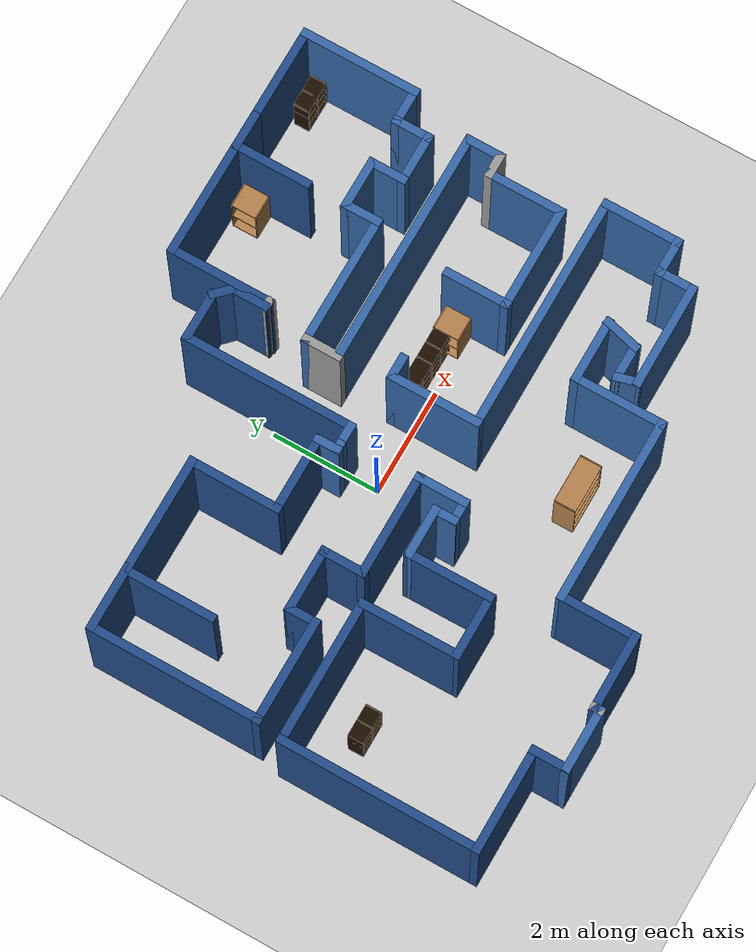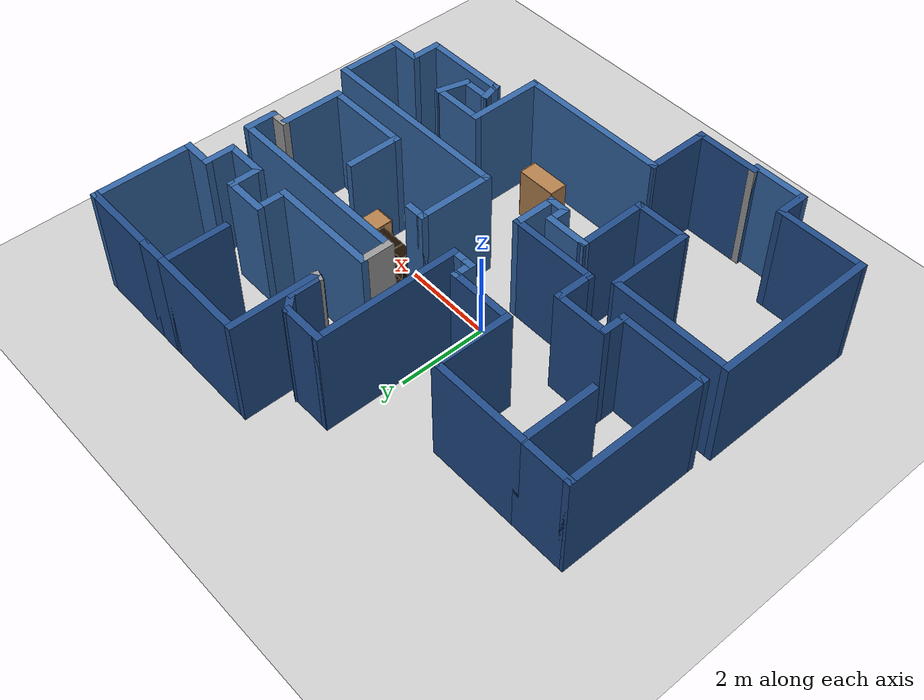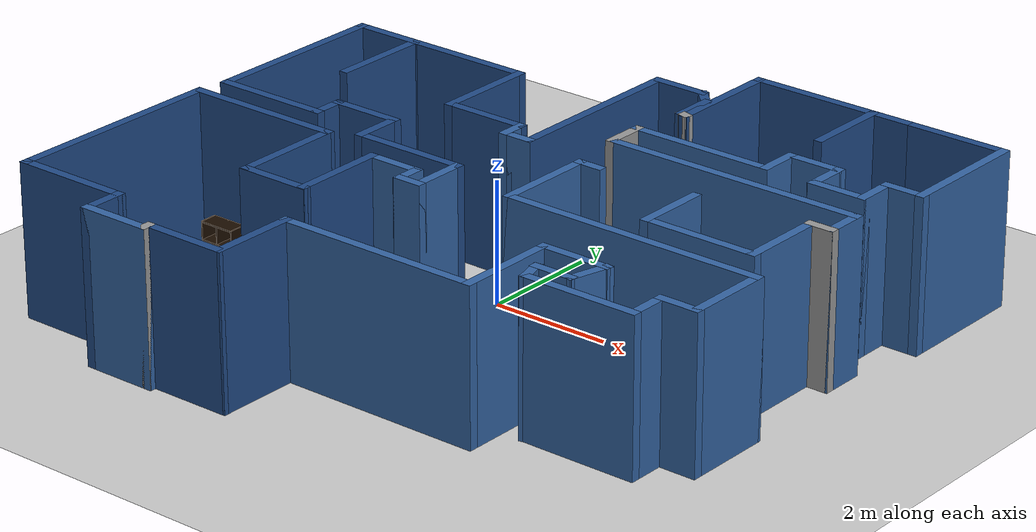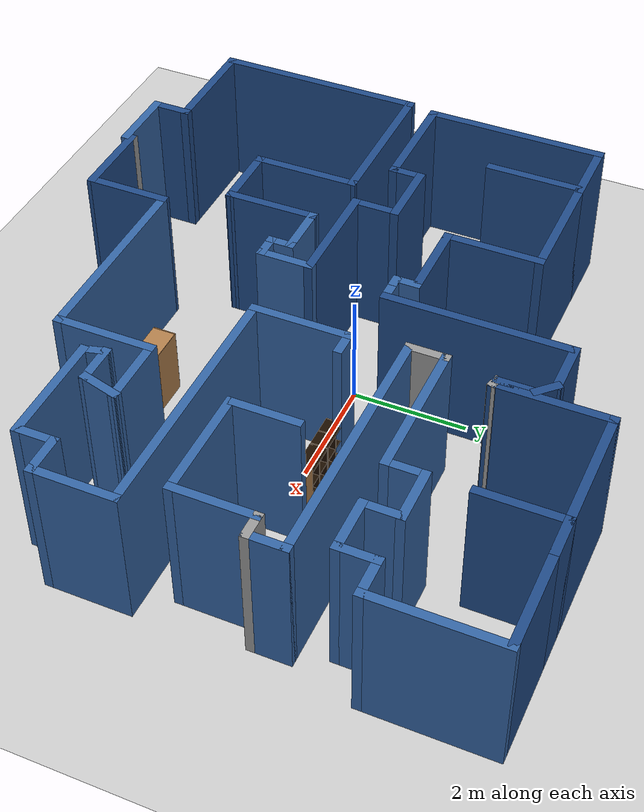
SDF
<sdf version="1.6">
 <world name="default">
  <light name="sun" type="directional">
   <pose>0 0 10 0 -0 0</pose>
   <diffuse>0.8 0.8 0.8 1</diffuse>
   <specular>0.2 0.2 0.2 1</specular>
   <attenuation>
    <range>1000</range>
    <constant>0.9</constant>
    <linear>0.01</linear>
    <quadratic>0.001</quadratic>
   </attenuation>
   <direction>-0.5 0.1 -0.9</direction>
  </light>
  <model name="ground_plane">
   <static>1</static>
   <link name="link">
    <collision name="collision">
     <geometry><plane><normal>0 0 1</normal><size>100 100</size></plane></geometry>
     <surface><friction><ode><mu>100</mu><mu2>50</mu2></ode></friction></surface>
    </collision>
    <visual name="visual">
     <cast_shadows>0</cast_shadows>
     <geometry><plane><normal>0 0 1</normal><size>100 100</size></plane></geometry>
     <material>
      <script><uri>file://media/materials/scripts/gazebo.material</uri><name>Gazebo/Grey</name></script>
     </material>
    </visual>
   </link>
  </model>
  <gravity>0 0 -9.8</gravity>
  <magnetic_field>6e-06 2.3e-05 -4.2e-05</magnetic_field>
  <atmosphere type="adiabatic"/>
  <physics name="default_physics" default="0" type="ode">
   <max_step_size>0.001</max_step_size>
   <real_time_factor>1</real_time_factor>
   <real_time_update_rate>1000</real_time_update_rate>
  </physics>
  <scene><ambient>0.4 0.4 0.4 1</ambient><background>0.7 0.7 0.7 1</background><shadows>1</shadows></scene>
  <spherical_coordinates>
   <surface_model>EARTH_WGS84</surface_model>
   <latitude_deg>0</latitude_deg>
   <longitude_deg>0</longitude_deg>
   <elevation>0</elevation>
   <heading_deg>0</heading_deg>
  </spherical_coordinates>
  <model name="map_5">
   <pose>0.379359 -0.317983 0 0 -0 0</pose>
   <link name="Wall_0">
    <collision name="Wall_0_Collision">
     <geometry><box><size>1.5 0.15 2.5</size></box></geometry>
     <pose>0 0 1.25 0 -0 0</pose>
    </collision>
    <visual name="Wall_0_Visual">
     <pose>0 0 1.25 0 -0 0</pose>
     <geometry><box><size>1.5 0.15 2.5</size></box></geometry>
     <material>
      <script><uri>file://media/materials/scripts/gazebo.material</uri><name>Gazebo/Grey</name></script>
      <ambient>0.12549 0.290196 0.529412 1</ambient>
     </material>
     <meta><layer>0</layer></meta>
    </visual>
    <pose>-1.72204 -4.86332 0 0 -0 3.14159</pose>
   </link>
   <link name="Wall_1">
    <collision name="Wall_1_Collision">
     <geometry><box><size>0.25 0.15 2.5</size></box></geometry>
     <pose>0 0 1.25 0 -0 0</pose>
    </collision>
    <visual name="Wall_1_Visual">
     <pose>0 0 1.25 0 -0 0</pose>
     <geometry><box><size>0.25 0.15 2.5</size></box></geometry>
     <material>
      <script><uri>file://media/materials/scripts/gazebo.material</uri><name>Gazebo/Grey</name></script>
      <ambient>1 1 1 1</ambient>
     </material>
     <meta><layer>0</layer></meta>
    </visual>
    <pose>-2.39704 -4.91331 0 0 -0 -1.5708</pose>
   </link>
   <link name="Wall_10">
    <collision name="Wall_10_Collision">
     <geometry><box><size>1 0.15 2.5</size></box></geometry>
     <pose>0 0 1.25 0 -0 0</pose>
    </collision>
    <visual name="Wall_10_Visual">
     <pose>0 0 1.25 0 -0 0</pose>
     <geometry><box><size>1 0.15 2.5</size></box></geometry>
     <material>
      <script><uri>file://media/materials/scripts/gazebo.material</uri><name>Gazebo/Grey</name></script>
      <ambient>0.203922 0.396078 0.643137 1</ambient>
     </material>
     <meta><layer>0</layer></meta>
    </visual>
    <pose>-1.22204 -1.01331 0 0 -0 0</pose>
   </link>
   <link name="Wall_11">
    <collision name="Wall_11_Collision">
     <geometry><box><size>0.5 0.15 2.5</size></box></geometry>
     <pose>0 0 1.25 0 -0 0</pose>
    </collision>
    <visual name="Wall_11_Visual">
     <pose>0 0 1.25 0 -0 0</pose>
     <geometry><box><size>0.5 0.15 2.5</size></box></geometry>
     <material>
      <script><uri>file://media/materials/scripts/gazebo.material</uri><name>Gazebo/Grey</name></script>
      <ambient>0.203922 0.396078 0.643137 1</ambient>
     </material>
     <meta><layer>0</layer></meta>
    </visual>
    <pose>-0.79704 -1.18832 0 0 -0 -1.5708</pose>
   </link>
   <link name="Wall_12">
    <collision name="Wall_12_Collision">
     <geometry><box><size>0.5 0.15 2.5</size></box></geometry>
     <pose>0 0 1.25 0 -0 0</pose>
    </collision>
    <visual name="Wall_12_Visual">
     <pose>0 0 1.25 0 -0 0</pose>
     <geometry><box><size>0.5 0.15 2.5</size></box></geometry>
     <material>
      <script><uri>file://media/materials/scripts/gazebo.material</uri><name>Gazebo/Grey</name></script>
      <ambient>0.203922 0.396078 0.643137 1</ambient>
     </material>
     <meta><layer>0</layer></meta>
    </visual>
    <pose>-0.62204 -1.36332 0 0 -0 0</pose>
   </link>
   <link name="Wall_13">
    <collision name="Wall_13_Collision">
     <geometry><box><size>1 0.15 2.5</size></box></geometry>
     <pose>0 0 1.25 0 -0 0</pose>
    </collision>
    <visual name="Wall_13_Visual">
     <pose>0 0 1.25 0 -0 0</pose>
     <geometry><box><size>1 0.15 2.5</size></box></geometry>
     <material>
      <script><uri>file://media/materials/scripts/gazebo.material</uri><name>Gazebo/Grey</name></script>
      <ambient>0.203922 0.396078 0.643137 1</ambient>
     </material>
     <meta><layer>0</layer></meta>
    </visual>
    <pose>-0.44704 -0.938315 0 0 -0 1.5708</pose>
   </link>
   <link name="Wall_14">
    <collision name="Wall_14_Collision">
     <geometry><box><size>2 0.15 2.5</size></box></geometry>
     <pose>0 0 1.25 0 -0 0</pose>
    </collision>
    <visual name="Wall_14_Visual">
     <pose>0 0 1.25 0 -0 0</pose>
     <geometry><box><size>2 0.15 2.5</size></box></geometry>
     <material>
      <script><uri>file://media/materials/scripts/gazebo.material</uri><name>Gazebo/Grey</name></script>
      <ambient>0.12549 0.290196 0.529412 1</ambient>
     </material>
     <meta><layer>0</layer></meta>
    </visual>
    <pose>-1.37204 -0.513315 0 0 -0 3.14159</pose>
   </link>
   <link name="Wall_15">
    <collision name="Wall_15_Collision">
     <geometry><box><size>0.847049 0.15 2.5</size></box></geometry>
     <pose>0 0 1.25 0 -0 0</pose>
    </collision>
    <visual name="Wall_15_Visual">
     <pose>0 0 1.25 0 -0 0</pose>
     <geometry><box><size>0.847049 0.15 2.5</size></box></geometry>
     <material>
      <script><uri>file://media/materials/scripts/gazebo.material</uri><name>Gazebo/Grey</name></script>
      <ambient>0.12549 0.290196 0.529412 1</ambient>
     </material>
     <meta><layer>0</layer></meta>
    </visual>
    <pose>-2.29704 -0.164791 0 0 -0 1.5708</pose>
   </link>
   <link name="Wall_16">
    <collision name="Wall_16_Collision">
     <geometry><box><size>1.25 0.15 2.5</size></box></geometry>
     <pose>0 0 1.25 0 -0 0</pose>
    </collision>
    <visual name="Wall_16_Visual">
     <pose>0 0 1.25 0 -0 0</pose>
     <geometry><box><size>1.25 0.15 2.5</size></box></geometry>
     <material>
      <script><uri>file://media/materials/scripts/gazebo.material</uri><name>Gazebo/Grey</name></script>
      <ambient>0.12549 0.290196 0.529412 1</ambient>
     </material>
     <meta><layer>0</layer></meta>
    </visual>
    <pose>-2.84704 0.214324 0 0 -0 3.14159</pose>
   </link>
   <link name="Wall_17">
    <collision name="Wall_17_Collision">
     <geometry><box><size>0.597049 0.15 2.5</size></box></geometry>
     <pose>0 0 1.25 0 -0 0</pose>
    </collision>
    <visual name="Wall_17_Visual">
     <pose>0 0 1.25 0 -0 0</pose>
     <geometry><box><size>0.597049 0.15 2.5</size></box></geometry>
     <material>
      <script><uri>file://media/materials/scripts/gazebo.material</uri><name>Gazebo/Grey</name></script>
      <ambient>0.12549 0.290196 0.529412 1</ambient>
     </material>
     <meta><layer>0</layer></meta>
    </visual>
    <pose>-3.39704 -0.039791 0 0 -0 -1.5708</pose>
   </link>
   <link name="Wall_18">
    <collision name="Wall_18_Collision">
     <geometry><box><size>2 0.15 2.5</size></box></geometry>
     <pose>0 0 1.25 0 -0 0</pose>
    </collision>
    <visual name="Wall_18_Visual">
     <pose>0 0 1.25 0 -0 0</pose>
     <geometry><box><size>2 0.15 2.5</size></box></geometry>
     <material>
      <script><uri>file://media/materials/scripts/gazebo.material</uri><name>Gazebo/Grey</name></script>
      <ambient>0.12549 0.290196 0.529412 1</ambient>
     </material>
     <meta><layer>0</layer></meta>
    </visual>
    <pose>-4.32204 -0.263315 0 0 -0 3.14159</pose>
   </link>
   <link name="Wall_19">
    <collision name="Wall_19_Collision">
     <geometry><box><size>3.25 0.15 2.5</size></box></geometry>
     <pose>0 0 1.25 0 -0 0</pose>
    </collision>
    <visual name="Wall_19_Visual">
     <pose>0 0 1.25 0 -0 0</pose>
     <geometry><box><size>3.25 0.15 2.5</size></box></geometry>
     <material>
      <script><uri>file://media/materials/scripts/gazebo.material</uri><name>Gazebo/Grey</name></script>
      <ambient>0.12549 0.290196 0.529412 1</ambient>
     </material>
     <meta><layer>0</layer></meta>
    </visual>
    <pose>-5.24704 1.28669 0 0 -0 1.5708</pose>
   </link>
   <link name="Wall_2">
    <collision name="Wall_2_Collision">
     <geometry><box><size>1.25 0.15 2.5</size></box></geometry>
     <pose>0 0 1.25 0 -0 0</pose>
    </collision>
    <visual name="Wall_2_Visual">
     <pose>0 0 1.25 0 -0 0</pose>
     <geometry><box><size>1.25 0.15 2.5</size></box></geometry>
     <material>
      <script><uri>file://media/materials/scripts/gazebo.material</uri><name>Gazebo/Grey</name></script>
      <ambient>0.203922 0.396078 0.643137 1</ambient>
     </material>
     <meta><layer>0</layer></meta>
    </visual>
    <pose>-2.94704 -4.96331 0 0 -0 3.14159</pose>
   </link>
   <link name="Wall_20">
    <collision name="Wall_20_Collision">
     <geometry><box><size>1.27531 0.15 2.5</size></box></geometry>
     <pose>0 0 1.25 0 -0 0</pose>
    </collision>
    <visual name="Wall_20_Visual">
     <pose>0 0 1.25 0 -0 0</pose>
     <geometry><box><size>1.27531 0.15 2.5</size></box></geometry>
     <material>
      <script><uri>file://media/materials/scripts/gazebo.material</uri><name>Gazebo/Grey</name></script>
      <ambient>0.12549 0.290196 0.529412 1</ambient>
     </material>
     <meta><layer>0</layer></meta>
    </visual>
    <pose>-4.68438 2.83669 0 0 -0 0</pose>
   </link>
   <link name="Wall_21">
    <collision name="Wall_21_Collision">
     <geometry><box><size>1.75 0.15 2.5</size></box></geometry>
     <pose>0 0 1.25 0 -0 0</pose>
    </collision>
    <visual name="Wall_21_Visual">
     <pose>0 0 1.25 0 -0 0</pose>
     <geometry><box><size>1.75 0.15 2.5</size></box></geometry>
     <material>
      <script><uri>file://media/materials/scripts/gazebo.material</uri><name>Gazebo/Grey</name></script>
      <ambient>0.12549 0.290196 0.529412 1</ambient>
     </material>
     <meta><layer>0</layer></meta>
    </visual>
    <pose>-4.15232 2.03668 0 0 -0 -1.5708</pose>
   </link>
   <link name="Wall_23">
    <collision name="Wall_23_Collision">
     <geometry><box><size>2.22469 0.15 2.5</size></box></geometry>
     <pose>0 0 1.25 0 -0 0</pose>
    </collision>
    <visual name="Wall_23_Visual">
     <pose>0 0 1.25 0 -0 0</pose>
     <geometry><box><size>2.22469 0.15 2.5</size></box></geometry>
     <material>
      <script><uri>file://media/materials/scripts/gazebo.material</uri><name>Gazebo/Grey</name></script>
      <ambient>0.12549 0.290196 0.529412 1</ambient>
     </material>
     <meta><layer>0</layer></meta>
    </visual>
    <pose>-3.08438 2.83669 0 0 -0 0</pose>
   </link>
   <link name="Wall_27">
    <collision name="Wall_27_Collision">
     <geometry><box><size>1.75 0.15 2.5</size></box></geometry>
     <pose>0 0 1.25 0 -0 0</pose>
    </collision>
    <visual name="Wall_27_Visual">
     <pose>0 0 1.25 0 -0 0</pose>
     <geometry><box><size>1.75 0.15 2.5</size></box></geometry>
     <material>
      <script><uri>file://media/materials/scripts/gazebo.material</uri><name>Gazebo/Grey</name></script>
      <ambient>0.12549 0.290196 0.529412 1</ambient>
     </material>
     <meta><layer>0</layer></meta>
    </visual>
    <pose>-2.04704 2.03668 0 0 -0 -1.5708</pose>
   </link>
   <link name="Wall_28">
    <collision name="Wall_28_Collision">
     <geometry><box><size>1.5 0.15 2.5</size></box></geometry>
     <pose>0 0 1.25 0 -0 0</pose>
    </collision>
    <visual name="Wall_28_Visual">
     <pose>0 0 1.25 0 -0 0</pose>
     <geometry><box><size>1.5 0.15 2.5</size></box></geometry>
     <material>
      <script><uri>file://media/materials/scripts/gazebo.material</uri><name>Gazebo/Grey</name></script>
      <ambient>0.12549 0.290196 0.529412 1</ambient>
     </material>
     <meta><layer>0</layer></meta>
    </visual>
    <pose>-1.37204 1.23669 0 0 -0 0</pose>
   </link>
   <link name="Wall_29">
    <collision name="Wall_29_Collision">
     <geometry><box><size>0.5 0.15 2.5</size></box></geometry>
     <pose>0 0 1.25 0 -0 0</pose>
    </collision>
    <visual name="Wall_29_Visual">
     <pose>0 0 1.25 0 -0 0</pose>
     <geometry><box><size>0.5 0.15 2.5</size></box></geometry>
     <material>
      <script><uri>file://media/materials/scripts/gazebo.material</uri><name>Gazebo/Grey</name></script>
      <ambient>0.203922 0.396078 0.643137 1</ambient>
     </material>
     <meta><layer>0</layer></meta>
    </visual>
    <pose>-0.69704 1.06168 0 0 -0 -1.5708</pose>
   </link>
   <link name="Wall_3">
    <collision name="Wall_3_Collision">
     <geometry><box><size>0.75 0.15 2.5</size></box></geometry>
     <pose>0 0 1.25 0 -0 0</pose>
    </collision>
    <visual name="Wall_3_Visual">
     <pose>0 0 1.25 0 -0 0</pose>
     <geometry><box><size>0.75 0.15 2.5</size></box></geometry>
     <material>
      <script><uri>file://media/materials/scripts/gazebo.material</uri><name>Gazebo/Grey</name></script>
      <ambient>0.12549 0.290196 0.529412 1</ambient>
     </material>
     <meta><layer>0</layer></meta>
    </visual>
    <pose>-3.49704 -4.66331 0 0 -0 1.5708</pose>
   </link>
   <link name="Wall_30">
    <collision name="Wall_30_Collision">
     <geometry><box><size>0.25 0.15 2.5</size></box></geometry>
     <pose>0 0 1.25 0 -0 0</pose>
    </collision>
    <visual name="Wall_30_Visual">
     <pose>0 0 1.25 0 -0 0</pose>
     <geometry><box><size>0.25 0.15 2.5</size></box></geometry>
     <material>
      <script><uri>file://media/materials/scripts/gazebo.material</uri><name>Gazebo/Grey</name></script>
      <ambient>0.203922 0.396078 0.643137 1</ambient>
     </material>
     <meta><layer>0</layer></meta>
    </visual>
    <pose>-0.64704 0.886685 0 0 -0 0</pose>
   </link>
   <link name="Wall_31">
    <collision name="Wall_31_Collision">
     <geometry><box><size>0.5 0.15 2.5</size></box></geometry>
     <pose>0 0 1.25 0 -0 0</pose>
    </collision>
    <visual name="Wall_31_Visual">
     <pose>0 0 1.25 0 -0 0</pose>
     <geometry><box><size>0.5 0.15 2.5</size></box></geometry>
     <material>
      <script><uri>file://media/materials/scripts/gazebo.material</uri><name>Gazebo/Grey</name></script>
      <ambient>0.203922 0.396078 0.643137 1</ambient>
     </material>
     <meta><layer>0</layer></meta>
    </visual>
    <pose>-0.42204 0.886685 0 0 -0 0</pose>
   </link>
   <link name="Wall_32">
    <collision name="Wall_32_Collision">
     <geometry><box><size>3.25 0.15 2.5</size></box></geometry>
     <pose>0 0 1.25 0 -0 0</pose>
    </collision>
    <visual name="Wall_32_Visual">
     <pose>0 0 1.25 0 -0 0</pose>
     <geometry><box><size>3.25 0.15 2.5</size></box></geometry>
     <material>
      <script><uri>file://media/materials/scripts/gazebo.material</uri><name>Gazebo/Grey</name></script>
      <ambient>0.12549 0.290196 0.529412 1</ambient>
     </material>
     <meta><layer>0</layer></meta>
    </visual>
    <pose>-0.24704 2.43669 0 0 -0 1.5708</pose>
   </link>
   <link name="Wall_33">
    <collision name="Wall_33_Collision">
     <geometry><box><size>1 0.15 2.5</size></box></geometry>
     <pose>0 0 1.25 0 -0 0</pose>
    </collision>
    <visual name="Wall_33_Visual">
     <pose>0 0 1.25 0 -0 0</pose>
     <geometry><box><size>1 0.15 2.5</size></box></geometry>
     <material>
      <script><uri>file://media/materials/scripts/gazebo.material</uri><name>Gazebo/Grey</name></script>
      <ambient>0.12549 0.290196 0.529412 1</ambient>
     </material>
     <meta><layer>0</layer></meta>
    </visual>
    <pose>0.17796 3.98669 0 0 -0 0</pose>
   </link>
   <link name="Wall_34">
    <collision name="Wall_34_Collision">
     <geometry><box><size>0.5 0.15 2.5</size></box></geometry>
     <pose>0 0 1.25 0 -0 0</pose>
    </collision>
    <visual name="Wall_34_Visual">
     <pose>0 0 1.25 0 -0 0</pose>
     <geometry><box><size>0.5 0.15 2.5</size></box></geometry>
     <material>
      <script><uri>file://media/materials/scripts/gazebo.material</uri><name>Gazebo/Grey</name></script>
      <ambient>0.12549 0.290196 0.529412 1</ambient>
     </material>
     <meta><layer>0</layer></meta>
    </visual>
    <pose>0.726704 3.86294 0 0 -0 -0.785398</pose>
   </link>
   <link name="Wall_35">
    <collision name="Wall_35_Collision">
     <geometry><box><size>0.75 0.15 2.5</size></box></geometry>
     <pose>0 0 1.25 0 -0 0</pose>
    </collision>
    <visual name="Wall_35_Visual">
     <pose>0 0 1.25 0 -0 0</pose>
     <geometry><box><size>0.75 0.15 2.5</size></box></geometry>
     <material>
      <script><uri>file://media/materials/scripts/gazebo.material</uri><name>Gazebo/Grey</name></script>
      <ambient>0.12549 0.290196 0.529412 1</ambient>
     </material>
     <meta><layer>0</layer></meta>
    </visual>
    <pose>0.850447 3.4392 0 0 -0 -1.5708</pose>
   </link>
   <link name="Wall_36">
    <collision name="Wall_36_Collision">
     <geometry><box><size>0.25 0.15 2.5</size></box></geometry>
     <pose>0 0 1.25 0 -0 0</pose>
    </collision>
    <visual name="Wall_36_Visual">
     <pose>0 0 1.25 0 -0 0</pose>
     <geometry><box><size>0.25 0.15 2.5</size></box></geometry>
     <material>
      <script><uri>file://media/materials/scripts/gazebo.material</uri><name>Gazebo/Grey</name></script>
      <ambient>1 1 1 1</ambient>
     </material>
     <meta><layer>0</layer></meta>
    </visual>
    <pose>0.898744 3.12626 0 0 -0 -0.261799</pose>
   </link>
   <link name="Wall_37">
    <collision name="Wall_37_Collision">
     <geometry><box><size>2 0.15 2.5</size></box></geometry>
     <pose>0 0 1.25 0 -0 0</pose>
    </collision>
    <visual name="Wall_37_Visual">
     <pose>0 0 1.25 0 -0 0</pose>
     <geometry><box><size>2 0.15 2.5</size></box></geometry>
     <material>
      <script><uri>file://media/materials/scripts/gazebo.material</uri><name>Gazebo/Grey</name></script>
      <ambient>0.12549 0.290196 0.529412 1</ambient>
     </material>
     <meta><layer>0</layer></meta>
    </visual>
    <pose>0.94704 4.03831 0 0 -0 1.5708</pose>
   </link>
   <link name="Wall_38">
    <collision name="Wall_38_Collision">
     <geometry><box><size>2.25 0.15 2.5</size></box></geometry>
     <pose>0 0 1.25 0 -0 0</pose>
    </collision>
    <visual name="Wall_38_Visual">
     <pose>0 0 1.25 0 -0 0</pose>
     <geometry><box><size>2.25 0.15 2.5</size></box></geometry>
     <material>
      <script><uri>file://media/materials/scripts/gazebo.material</uri><name>Gazebo/Grey</name></script>
      <ambient>0.12549 0.290196 0.529412 1</ambient>
     </material>
     <meta><layer>0</layer></meta>
    </visual>
    <pose>1.99704 4.96331 0 0 -0 0</pose>
   </link>
   <link name="Wall_39">
    <collision name="Wall_39_Collision">
     <geometry><box><size>1.5 0.15 2.5</size></box></geometry>
     <pose>0 0 1.25 0 -0 0</pose>
    </collision>
    <visual name="Wall_39_Visual">
     <pose>0 0 1.25 0 -0 0</pose>
     <geometry><box><size>1.5 0.15 2.5</size></box></geometry>
     <material>
      <script><uri>file://media/materials/scripts/gazebo.material</uri><name>Gazebo/Grey</name></script>
      <ambient>0.12549 0.290196 0.529412 1</ambient>
     </material>
     <meta><layer>0</layer></meta>
    </visual>
    <pose>3.04704 4.28831 0 0 -0 -1.5708</pose>
   </link>
   <link name="Wall_4">
    <collision name="Wall_4_Collision">
     <geometry><box><size>2 0.15 2.5</size></box></geometry>
     <pose>0 0 1.25 0 -0 0</pose>
    </collision>
    <visual name="Wall_4_Visual">
     <pose>0 0 1.25 0 -0 0</pose>
     <geometry><box><size>2 0.15 2.5</size></box></geometry>
     <material>
      <script><uri>file://media/materials/scripts/gazebo.material</uri><name>Gazebo/Grey</name></script>
      <ambient>0.12549 0.290196 0.529412 1</ambient>
     </material>
     <meta><layer>0</layer></meta>
    </visual>
    <pose>-4.42204 -4.36332 0 0 -0 3.14159</pose>
   </link>
   <link name="Wall_41">
    <collision name="Wall_41_Collision">
     <geometry><box><size>0.75 0.15 2.5</size></box></geometry>
     <pose>0 0 1.25 0 -0 0</pose>
    </collision>
    <visual name="Wall_41_Visual">
     <pose>0 0 1.25 0 -0 0</pose>
     <geometry><box><size>0.75 0.15 2.5</size></box></geometry>
     <material>
      <script><uri>file://media/materials/scripts/gazebo.material</uri><name>Gazebo/Grey</name></script>
      <ambient>0.12549 0.290196 0.529412 1</ambient>
     </material>
     <meta><layer>0</layer></meta>
    </visual>
    <pose>3.34704 4.96331 0 0 -0 0</pose>
   </link>
   <link name="Wall_46">
    <collision name="Wall_46_Collision">
     <geometry><box><size>2.25 0.15 2.5</size></box></geometry>
     <pose>0 0 1.25 0 -0 0</pose>
    </collision>
    <visual name="Wall_46_Visual">
     <pose>0 0 1.25 0 -0 0</pose>
     <geometry><box><size>2.25 0.15 2.5</size></box></geometry>
     <material>
      <script><uri>file://media/materials/scripts/gazebo.material</uri><name>Gazebo/Grey</name></script>
      <ambient>0.203922 0.396078 0.643137 1</ambient>
     </material>
     <meta><layer>0</layer></meta>
    </visual>
    <pose>5.34704 3.91331 0 0 -0 -1.5708</pose>
   </link>
   <link name="Wall_47">
    <collision name="Wall_47_Collision">
     <geometry><box><size>0.75 0.15 2.5</size></box></geometry>
     <pose>0 0 1.25 0 -0 0</pose>
    </collision>
    <visual name="Wall_47_Visual">
     <pose>0 0 1.25 0 -0 0</pose>
     <geometry><box><size>0.75 0.15 2.5</size></box></geometry>
     <material>
      <script><uri>file://media/materials/scripts/gazebo.material</uri><name>Gazebo/Grey</name></script>
      <ambient>0.203922 0.396078 0.643137 1</ambient>
     </material>
     <meta><layer>0</layer></meta>
    </visual>
    <pose>5.04704 2.86332 0 0 -0 3.14159</pose>
   </link>
   <link name="Wall_48">
    <collision name="Wall_48_Collision">
     <geometry><box><size>0.75 0.15 2.5</size></box></geometry>
     <pose>0 0 1.25 0 -0 0</pose>
    </collision>
    <visual name="Wall_48_Visual">
     <pose>0 0 1.25 0 -0 0</pose>
     <geometry><box><size>0.75 0.15 2.5</size></box></geometry>
     <material>
      <script><uri>file://media/materials/scripts/gazebo.material</uri><name>Gazebo/Grey</name></script>
      <ambient>0.203922 0.396078 0.643137 1</ambient>
     </material>
     <meta><layer>0</layer></meta>
    </visual>
    <pose>4.74704 2.56331 0 0 -0 -1.5708</pose>
   </link>
   <link name="Wall_49">
    <collision name="Wall_49_Collision">
     <geometry><box><size>1 0.15 2.5</size></box></geometry>
     <pose>0 0 1.25 0 -0 0</pose>
    </collision>
    <visual name="Wall_49_Visual">
     <pose>0 0 1.25 0 -0 0</pose>
     <geometry><box><size>1 0.15 2.5</size></box></geometry>
     <material>
      <script><uri>file://media/materials/scripts/gazebo.material</uri><name>Gazebo/Grey</name></script>
      <ambient>0.203922 0.396078 0.643137 1</ambient>
     </material>
     <meta><layer>0</layer></meta>
    </visual>
    <pose>4.32204 2.26331 0 0 -0 3.14159</pose>
   </link>
   <link name="Wall_5">
    <collision name="Wall_5_Collision">
     <geometry><box><size>3.75 0.15 2.5</size></box></geometry>
     <pose>0 0 1.25 0 -0 0</pose>
    </collision>
    <visual name="Wall_5_Visual">
     <pose>0 0 1.25 0 -0 0</pose>
     <geometry><box><size>3.75 0.15 2.5</size></box></geometry>
     <material>
      <script><uri>file://media/materials/scripts/gazebo.material</uri><name>Gazebo/Grey</name></script>
      <ambient>0.12549 0.290196 0.529412 1</ambient>
     </material>
     <meta><layer>0</layer></meta>
    </visual>
    <pose>-5.34704 -2.56331 0 0 -0 1.5708</pose>
   </link>
   <link name="Wall_50">
    <collision name="Wall_50_Collision">
     <geometry><box><size>0.75 0.15 2.5</size></box></geometry>
     <pose>0 0 1.25 0 -0 0</pose>
    </collision>
    <visual name="Wall_50_Visual">
     <pose>0 0 1.25 0 -0 0</pose>
     <geometry><box><size>0.75 0.15 2.5</size></box></geometry>
     <material>
      <script><uri>file://media/materials/scripts/gazebo.material</uri><name>Gazebo/Grey</name></script>
      <ambient>0.203922 0.396078 0.643137 1</ambient>
     </material>
     <meta><layer>0</layer></meta>
    </visual>
    <pose>3.89704 2.56331 0 0 -0 1.5708</pose>
   </link>
   <link name="Wall_51">
    <collision name="Wall_51_Collision">
     <geometry><box><size>1 0.15 2.5</size></box></geometry>
     <pose>0 0 1.25 0 -0 0</pose>
    </collision>
    <visual name="Wall_51_Visual">
     <pose>0 0 1.25 0 -0 0</pose>
     <geometry><box><size>1 0.15 2.5</size></box></geometry>
     <material>
      <script><uri>file://media/materials/scripts/gazebo.material</uri><name>Gazebo/Grey</name></script>
      <ambient>0.203922 0.396078 0.643137 1</ambient>
     </material>
     <meta><layer>0</layer></meta>
    </visual>
    <pose>3.47204 2.86332 0 0 -0 3.14159</pose>
   </link>
   <link name="Wall_52">
    <collision name="Wall_52_Collision">
     <geometry><box><size>0.75 0.15 2.5</size></box></geometry>
     <pose>0 0 1.25 0 -0 0</pose>
    </collision>
    <visual name="Wall_52_Visual">
     <pose>0 0 1.25 0 -0 0</pose>
     <geometry><box><size>0.75 0.15 2.5</size></box></geometry>
     <material>
      <script><uri>file://media/materials/scripts/gazebo.material</uri><name>Gazebo/Grey</name></script>
      <ambient>0.203922 0.396078 0.643137 1</ambient>
     </material>
     <meta><layer>0</layer></meta>
    </visual>
    <pose>3.04704 2.56331 0 0 -0 -1.5708</pose>
   </link>
   <link name="Wall_53">
    <collision name="Wall_53_Collision">
     <geometry><box><size>2.5 0.15 2.5</size></box></geometry>
     <pose>0 0 1.25 0 -0 0</pose>
    </collision>
    <visual name="Wall_53_Visual">
     <pose>0 0 1.25 0 -0 0</pose>
     <geometry><box><size>2.5 0.15 2.5</size></box></geometry>
     <material>
      <script><uri>file://media/materials/scripts/gazebo.material</uri><name>Gazebo/Grey</name></script>
      <ambient>0.203922 0.396078 0.643137 1</ambient>
     </material>
     <meta><layer>0</layer></meta>
    </visual>
    <pose>1.87204 2.26331 0 0 -0 3.14159</pose>
   </link>
   <link name="Wall_54">
    <collision name="Wall_54_Collision">
     <geometry><box><size>0.75 0.15 2.5</size></box></geometry>
     <pose>0 0 1.25 0 -0 0</pose>
    </collision>
    <visual name="Wall_54_Visual">
     <pose>0 0 1.25 0 -0 0</pose>
     <geometry><box><size>0.75 0.15 2.5</size></box></geometry>
     <material>
      <script><uri>file://media/materials/scripts/gazebo.material</uri><name>Gazebo/Grey</name></script>
      <ambient>1 1 1 1</ambient>
     </material>
     <meta><layer>0</layer></meta>
    </visual>
    <pose>0.69704 1.96331 0 0 -0 -1.5708</pose>
   </link>
   <link name="Wall_55">
    <collision name="Wall_55_Collision">
     <geometry><box><size>4.5 0.15 2.5</size></box></geometry>
     <pose>0 0 1.25 0 -0 0</pose>
    </collision>
    <visual name="Wall_55_Visual">
     <pose>0 0 1.25 0 -0 0</pose>
     <geometry><box><size>4.5 0.15 2.5</size></box></geometry>
     <material>
      <script><uri>file://media/materials/scripts/gazebo.material</uri><name>Gazebo/Grey</name></script>
      <ambient>0.203922 0.396078 0.643137 1</ambient>
     </material>
     <meta><layer>0</layer></meta>
    </visual>
    <pose>2.87204 1.66332 0 0 -0 0</pose>
   </link>
   <link name="Wall_56">
    <collision name="Wall_56_Collision">
     <geometry><box><size>0.75 0.15 2.5</size></box></geometry>
     <pose>0 0 1.25 0 -0 0</pose>
    </collision>
    <visual name="Wall_56_Visual">
     <pose>0 0 1.25 0 -0 0</pose>
     <geometry><box><size>0.75 0.15 2.5</size></box></geometry>
     <material>
      <script><uri>file://media/materials/scripts/gazebo.material</uri><name>Gazebo/Grey</name></script>
      <ambient>0.203922 0.396078 0.643137 1</ambient>
     </material>
     <meta><layer>0</layer></meta>
    </visual>
    <pose>5.04704 1.36332 0 0 -0 -1.5708</pose>
   </link>
   <link name="Wall_57">
    <collision name="Wall_57_Collision">
     <geometry><box><size>0.5 0.15 2.5</size></box></geometry>
     <pose>0 0 1.25 0 -0 0</pose>
    </collision>
    <visual name="Wall_57_Visual">
     <pose>0 0 1.25 0 -0 0</pose>
     <geometry><box><size>0.5 0.15 2.5</size></box></geometry>
     <material>
      <script><uri>file://media/materials/scripts/gazebo.material</uri><name>Gazebo/Grey</name></script>
      <ambient>1 1 1 1</ambient>
     </material>
     <meta><layer>0</layer></meta>
    </visual>
    <pose>4.87204 1.06332 0 0 -0 3.14159</pose>
   </link>
   <link name="Wall_58">
    <collision name="Wall_58_Collision">
     <geometry><box><size>1.5 0.15 2.5</size></box></geometry>
     <pose>0 0 1.25 0 -0 0</pose>
    </collision>
    <visual name="Wall_58_Visual">
     <pose>0 0 1.25 0 -0 0</pose>
     <geometry><box><size>1.5 0.15 2.5</size></box></geometry>
     <material>
      <script><uri>file://media/materials/scripts/gazebo.material</uri><name>Gazebo/Grey</name></script>
      <ambient>0.203922 0.396078 0.643137 1</ambient>
     </material>
     <meta><layer>0</layer></meta>
    </visual>
    <pose>4.69704 0.388315 0 0 -0 -1.5708</pose>
   </link>
   <link name="Wall_59">
    <collision name="Wall_59_Collision">
     <geometry><box><size>2 0.15 2.5</size></box></geometry>
     <pose>0 0 1.25 0 -0 0</pose>
    </collision>
    <visual name="Wall_59_Visual">
     <pose>0 0 1.25 0 -0 0</pose>
     <geometry><box><size>2 0.15 2.5</size></box></geometry>
     <material>
      <script><uri>file://media/materials/scripts/gazebo.material</uri><name>Gazebo/Grey</name></script>
      <ambient>0.203922 0.396078 0.643137 1</ambient>
     </material>
     <meta><layer>0</layer></meta>
    </visual>
    <pose>3.77204 -0.286685 0 0 -0 3.14159</pose>
   </link>
   <link name="Wall_6">
    <collision name="Wall_6_Collision">
     <geometry><box><size>2.75 0.15 2.5</size></box></geometry>
     <pose>0 0 1.25 0 -0 0</pose>
    </collision>
    <visual name="Wall_6_Visual">
     <pose>0 0 1.25 0 -0 0</pose>
     <geometry><box><size>2.75 0.15 2.5</size></box></geometry>
     <material>
      <script><uri>file://media/materials/scripts/gazebo.material</uri><name>Gazebo/Grey</name></script>
      <ambient>0.12549 0.290196 0.529412 1</ambient>
     </material>
     <meta><layer>0</layer></meta>
    </visual>
    <pose>-4.04704 -0.763315 0 0 -0 0</pose>
   </link>
   <link name="Wall_60">
    <collision name="Wall_60_Collision">
     <geometry><box><size>1.25 0.15 2.5</size></box></geometry>
     <pose>0 0 1.25 0 -0 0</pose>
    </collision>
    <visual name="Wall_60_Visual">
     <pose>0 0 1.25 0 -0 0</pose>
     <geometry><box><size>1.25 0.15 2.5</size></box></geometry>
     <material>
      <script><uri>file://media/materials/scripts/gazebo.material</uri><name>Gazebo/Grey</name></script>
      <ambient>0.203922 0.396078 0.643137 1</ambient>
     </material>
     <meta><layer>0</layer></meta>
    </visual>
    <pose>2.84704 0.263315 0 0 -0 1.5708</pose>
   </link>
   <link name="Wall_64">
    <collision name="Wall_64_Collision">
     <geometry><box><size>0.5 0.15 2.5</size></box></geometry>
     <pose>0 0 1.25 0 -0 0</pose>
    </collision>
    <visual name="Wall_64_Visual">
     <pose>0 0 1.25 0 -0 0</pose>
     <geometry><box><size>0.5 0.15 2.5</size></box></geometry>
     <material>
      <script><uri>file://media/materials/scripts/gazebo.material</uri><name>Gazebo/Grey</name></script>
      <ambient>0.203922 0.396078 0.643137 1</ambient>
     </material>
     <meta><layer>0</layer></meta>
    </visual>
    <pose>1.01362 0.726503 0 0 -0 3.14159</pose>
   </link>
   <link name="Wall_65">
    <collision name="Wall_65_Collision">
     <geometry><box><size>1.75 0.15 2.5</size></box></geometry>
     <pose>0 0 1.25 0 -0 0</pose>
    </collision>
    <visual name="Wall_65_Visual">
     <pose>0 0 1.25 0 -0 0</pose>
     <geometry><box><size>1.75 0.15 2.5</size></box></geometry>
     <material>
      <script><uri>file://media/materials/scripts/gazebo.material</uri><name>Gazebo/Grey</name></script>
      <ambient>0.203922 0.396078 0.643137 1</ambient>
     </material>
     <meta><layer>0</layer></meta>
    </visual>
    <pose>0.838617 -0.073497 0 0 -0 -1.5708</pose>
   </link>
   <link name="Wall_66">
    <collision name="Wall_66_Collision">
     <geometry><box><size>4.5 0.15 2.5</size></box></geometry>
     <pose>0 0 1.25 0 -0 0</pose>
    </collision>
    <visual name="Wall_66_Visual">
     <pose>0 0 1.25 0 -0 0</pose>
     <geometry><box><size>4.5 0.15 2.5</size></box></geometry>
     <material>
      <script><uri>file://media/materials/scripts/gazebo.material</uri><name>Gazebo/Grey</name></script>
      <ambient>0.203922 0.396078 0.643137 1</ambient>
     </material>
     <meta><layer>0</layer></meta>
    </visual>
    <pose>3.01362 -0.873497 0 0 -0 0</pose>
   </link>
   <link name="Wall_67">
    <collision name="Wall_67_Collision">
     <geometry><box><size>1.5 0.15 2.5</size></box></geometry>
     <pose>0 0 1.25 0 -0 0</pose>
    </collision>
    <visual name="Wall_67_Visual">
     <pose>0 0 1.25 0 -0 0</pose>
     <geometry><box><size>1.5 0.15 2.5</size></box></geometry>
     <material>
      <script><uri>file://media/materials/scripts/gazebo.material</uri><name>Gazebo/Grey</name></script>
      <ambient>0.203922 0.396078 0.643137 1</ambient>
     </material>
     <meta><layer>0</layer></meta>
    </visual>
    <pose>5.18862 -1.5485 0 0 -0 -1.5708</pose>
   </link>
   <link name="Wall_68">
    <collision name="Wall_68_Collision">
     <geometry><box><size>0.75 0.15 2.5</size></box></geometry>
     <pose>0 0 1.25 0 -0 0</pose>
    </collision>
    <visual name="Wall_68_Visual">
     <pose>0 0 1.25 0 -0 0</pose>
     <geometry><box><size>0.75 0.15 2.5</size></box></geometry>
     <material>
      <script><uri>file://media/materials/scripts/gazebo.material</uri><name>Gazebo/Grey</name></script>
      <ambient>0.203922 0.396078 0.643137 1</ambient>
     </material>
     <meta><layer>0</layer></meta>
    </visual>
    <pose>4.88862 -2.2235 0 0 -0 3.14159</pose>
   </link>
   <link name="Wall_69">
    <collision name="Wall_69_Collision">
     <geometry><box><size>0.75 0.15 2.5</size></box></geometry>
     <pose>0 0 1.25 0 -0 0</pose>
    </collision>
    <visual name="Wall_69_Visual">
     <pose>0 0 1.25 0 -0 0</pose>
     <geometry><box><size>0.75 0.15 2.5</size></box></geometry>
     <material>
      <script><uri>file://media/materials/scripts/gazebo.material</uri><name>Gazebo/Grey</name></script>
      <ambient>0.203922 0.396078 0.643137 1</ambient>
     </material>
     <meta><layer>0</layer></meta>
    </visual>
    <pose>4.58862 -2.5235 0 0 -0 -1.5708</pose>
   </link>
   <link name="Wall_7">
    <collision name="Wall_7_Collision">
     <geometry><box><size>1.88506 0.15 2.5</size></box></geometry>
     <pose>0 0 1.25 0 -0 0</pose>
    </collision>
    <visual name="Wall_7_Visual">
     <pose>0 0 1.25 0 -0 0</pose>
     <geometry><box><size>1.88506 0.15 2.5</size></box></geometry>
     <material>
      <script><uri>file://media/materials/scripts/gazebo.material</uri><name>Gazebo/Grey</name></script>
      <ambient>0.12549 0.290196 0.529412 1</ambient>
     </material>
     <meta><layer>0</layer></meta>
    </visual>
    <pose>-2.73944 -1.63081 0 0 -0 -1.56203</pose>
   </link>
   <link name="Wall_70">
    <collision name="Wall_70_Collision">
     <geometry><box><size>2 0.15 2.5</size></box></geometry>
     <pose>0 0 1.25 0 -0 0</pose>
    </collision>
    <visual name="Wall_70_Visual">
     <pose>0 0 1.25 0 -0 0</pose>
     <geometry><box><size>2 0.15 2.5</size></box></geometry>
     <material>
      <script><uri>file://media/materials/scripts/gazebo.material</uri><name>Gazebo/Grey</name></script>
      <ambient>0.203922 0.396078 0.643137 1</ambient>
     </material>
     <meta><layer>0</layer></meta>
    </visual>
    <pose>3.66362 -2.8235 0 0 -0 3.14159</pose>
   </link>
   <link name="Wall_71">
    <collision name="Wall_71_Collision">
     <geometry><box><size>0.5 0.15 2.5</size></box></geometry>
     <pose>0 0 1.25 0 -0 0</pose>
    </collision>
    <visual name="Wall_71_Visual">
     <pose>0 0 1.25 0 -0 0</pose>
     <geometry><box><size>0.5 0.15 2.5</size></box></geometry>
     <material>
      <script><uri>file://media/materials/scripts/gazebo.material</uri><name>Gazebo/Grey</name></script>
      <ambient>0.203922 0.396078 0.643137 1</ambient>
     </material>
     <meta><layer>0</layer></meta>
    </visual>
    <pose>2.69332 -2.65446 0 0 -0 1.8326</pose>
   </link>
   <link name="Wall_72">
    <collision name="Wall_72_Collision">
     <geometry><box><size>0.75 0.15 2.5</size></box></geometry>
     <pose>0 0 1.25 0 -0 0</pose>
    </collision>
    <visual name="Wall_72_Visual">
     <pose>0 0 1.25 0 -0 0</pose>
     <geometry><box><size>0.75 0.15 2.5</size></box></geometry>
     <material>
      <script><uri>file://media/materials/scripts/gazebo.material</uri><name>Gazebo/Grey</name></script>
      <ambient>0.203922 0.396078 0.643137 1</ambient>
     </material>
     <meta><layer>0</layer></meta>
    </visual>
    <pose>2.94803 -2.48542 0 0 -0 0</pose>
   </link>
   <link name="Wall_73">
    <collision name="Wall_73_Collision">
     <geometry><box><size>0.75 0.15 2.5</size></box></geometry>
     <pose>0 0 1.25 0 -0 0</pose>
    </collision>
    <visual name="Wall_73_Visual">
     <pose>0 0 1.25 0 -0 0</pose>
     <geometry><box><size>0.75 0.15 2.5</size></box></geometry>
     <material>
      <script><uri>file://media/materials/scripts/gazebo.material</uri><name>Gazebo/Grey</name></script>
      <ambient>0.203922 0.396078 0.643137 1</ambient>
     </material>
     <meta><layer>0</layer></meta>
    </visual>
    <pose>3.32568 -2.19564 0 0 -0 1.309</pose>
   </link>
   <link name="Wall_74">
    <collision name="Wall_74_Collision">
     <geometry><box><size>1.25 0.15 2.5</size></box></geometry>
     <pose>0 0 1.25 0 -0 0</pose>
    </collision>
    <visual name="Wall_74_Visual">
     <pose>0 0 1.25 0 -0 0</pose>
     <geometry><box><size>1.25 0.15 2.5</size></box></geometry>
     <material>
      <script><uri>file://media/materials/scripts/gazebo.material</uri><name>Gazebo/Grey</name></script>
      <ambient>0.203922 0.396078 0.643137 1</ambient>
     </material>
     <meta><layer>0</layer></meta>
    </visual>
    <pose>2.85332 -1.90587 0 0 -0 3.14159</pose>
   </link>
   <link name="Wall_76">
    <collision name="Wall_76_Collision">
     <geometry><box><size>1.85 0.15 2.5</size></box></geometry>
     <pose>0 0 1.25 0 -0 0</pose>
    </collision>
    <visual name="Wall_76_Visual">
     <pose>0 0 1.25 0 -0 0</pose>
     <geometry><box><size>1.85 0.15 2.5</size></box></geometry>
     <material>
      <script><uri>file://media/materials/scripts/gazebo.material</uri><name>Gazebo/Grey</name></script>
      <ambient>0.12549 0.290196 0.529412 1</ambient>
     </material>
     <meta><layer>0</layer></meta>
    </visual>
    <pose>4.49704 4.96331 0 0 -0 0</pose>
   </link>
   <link name="Wall_78">
    <collision name="Wall_78_Collision">
     <geometry><box><size>1.75 0.15 2.5</size></box></geometry>
     <pose>0 0 1.25 0 -0 0</pose>
    </collision>
    <visual name="Wall_78_Visual">
     <pose>0 0 1.25 0 -0 0</pose>
     <geometry><box><size>1.75 0.15 2.5</size></box></geometry>
     <material>
      <script><uri>file://media/materials/scripts/gazebo.material</uri><name>Gazebo/Grey</name></script>
      <ambient>0.203922 0.396078 0.643137 1</ambient>
     </material>
     <meta><layer>0</layer></meta>
    </visual>
    <pose>2.30332 -2.70587 0 0 -0 -1.5708</pose>
   </link>
   <link name="Wall_79">
    <collision name="Wall_79_Collision">
     <geometry><box><size>3.5 0.15 2.5</size></box></geometry>
     <pose>0 0 1.25 0 -0 0</pose>
    </collision>
    <visual name="Wall_79_Visual">
     <pose>0 0 1.25 0 -0 0</pose>
     <geometry><box><size>3.5 0.15 2.5</size></box></geometry>
     <material>
      <script><uri>file://media/materials/scripts/gazebo.material</uri><name>Gazebo/Grey</name></script>
      <ambient>0.203922 0.396078 0.643137 1</ambient>
     </material>
     <meta><layer>0</layer></meta>
    </visual>
    <pose>0.628322 -3.50587 0 0 -0 3.14159</pose>
   </link>
   <link name="Wall_8">
    <collision name="Wall_8_Collision">
     <geometry><box><size>1.25 0.15 2.5</size></box></geometry>
     <pose>0 0 1.25 0 -0 0</pose>
    </collision>
    <visual name="Wall_8_Visual">
     <pose>0 0 1.25 0 -0 0</pose>
     <geometry><box><size>1.25 0.15 2.5</size></box></geometry>
     <material>
      <script><uri>file://media/materials/scripts/gazebo.material</uri><name>Gazebo/Grey</name></script>
      <ambient>0.12549 0.290196 0.529412 1</ambient>
     </material>
     <meta><layer>0</layer></meta>
    </visual>
    <pose>-2.18183 -2.51351 0 0 -0 0</pose>
   </link>
   <link name="Wall_87">
    <collision name="Wall_87_Collision">
     <geometry><box><size>1.50745 0.15 2.5</size></box></geometry>
     <pose>0 0 1.25 0 -0 0</pose>
    </collision>
    <visual name="Wall_87_Visual">
     <pose>0 0 1.25 0 -0 0</pose>
     <geometry><box><size>1.50745 0.15 2.5</size></box></geometry>
     <material>
      <script><uri>file://media/materials/scripts/gazebo.material</uri><name>Gazebo/Grey</name></script>
      <ambient>0.12549 0.290196 0.529412 1</ambient>
     </material>
     <meta><layer>0</layer></meta>
    </visual>
    <pose>-1.04686 -4.18459 0 0 -0 -1.57106</pose>
   </link>
   <link name="Wall_9">
    <collision name="Wall_9_Collision">
     <geometry><box><size>1.63507 0.15 2.5</size></box></geometry>
     <pose>0 0 1.25 0 -0 0</pose>
    </collision>
    <visual name="Wall_9_Visual">
     <pose>0 0 1.25 0 -0 0</pose>
     <geometry><box><size>1.63507 0.15 2.5</size></box></geometry>
     <material>
      <script><uri>file://media/materials/scripts/gazebo.material</uri><name>Gazebo/Grey</name></script>
      <ambient>0.12549 0.290196 0.529412 1</ambient>
     </material>
     <meta><layer>0</layer></meta>
    </visual>
    <pose>-1.63944 -1.75581 0 0 -0 1.58104</pose>
   </link>
   <static>1</static>
  </model>
  <model name="6_Cube_StorageE">
   <link name="Wall_0">
    <pose>0 0 0.01 0 -0 0</pose>
    <inertial>
     <mass>1.6201</mass>
     <inertia><ixx>0.0119</ixx><iyy>0.0631</iyy><izz>0.0513</izz><ixy>0</ixy><ixz>0</ixz><iyz>0</iyz></inertia>
    </inertial>
    <collision name="Wall_0_Collision"><geometry><box><size>0.616 0.296 0.02</size></box></geometry></collision>
    <visual name="Wall_0_Visual">
     <geometry><box><size>0.616 0.296 0.02</size></box></geometry>
     <material>
      <script><uri>file://media/materials/scripts/gazebo.material</uri><name>Gazebo/Grey</name></script>
      <ambient>0.105882 0.0509804 0 1</ambient>
     </material>
    </visual>
   </link>
   <joint name="0_2" type="fixed">
    <pose>-0.308 0 0 0 -0 0</pose>
    <parent>Wall_2</parent>
    <child>Wall_0</child>
    <axis>
     <xyz>1 0 0</xyz>
     <use_parent_model_frame>0</use_parent_model_frame>
     <limit><lower>-1e+16</lower><upper>1e+16</upper></limit>
    </axis>
   </joint>
   <joint name="0_12" type="fixed">
    <parent>Wall_12</parent>
    <child>Wall_0</child>
    <axis>
     <xyz>0 0 1</xyz>
     <use_parent_model_frame>0</use_parent_model_frame>
     <limit><lower>-1e+16</lower><upper>1e+16</upper></limit>
    </axis>
   </joint>
   <joint name="0_4" type="fixed">
    <pose>0.308 0 0 0 -0 0</pose>
    <parent>Wall_4</parent>
    <child>Wall_0</child>
    <axis>
     <xyz>1 0 0</xyz>
     <use_parent_model_frame>0</use_parent_model_frame>
     <limit><lower>-1e+16</lower><upper>1e+16</upper></limit>
    </axis>
   </joint>
   <link name="Wall_10">
    <pose>0 0 0.61 0 -0 0</pose>
    <inertial>
     <mass>1.6201</mass>
     <inertia><ixx>0.0119</ixx><iyy>0.0631</iyy><izz>0.0513</izz><ixy>0</ixy><ixz>0</ixz><iyz>0</iyz></inertia>
    </inertial>
    <collision name="Wall_10_Collision"><geometry><box><size>0.616 0.296 0.02</size></box></geometry></collision>
    <visual name="Wall_10_Visual">
     <geometry><box><size>0.616 0.296 0.02</size></box></geometry>
     <material>
      <script><uri>file://media/materials/scripts/gazebo.material</uri><name>Gazebo/Grey</name></script>
      <ambient>0.105882 0.0509804 0 1</ambient>
     </material>
    </visual>
   </link>
   <joint name="10_2" type="fixed">
    <pose>-0.308 0 0 0 -0 0</pose>
    <parent>Wall_2</parent>
    <child>Wall_10</child>
    <axis>
     <xyz>1 0 0</xyz>
     <use_parent_model_frame>0</use_parent_model_frame>
     <limit><lower>-1e+16</lower><upper>1e+16</upper></limit>
    </axis>
   </joint>
   <joint name="10_12" type="fixed">
    <parent>Wall_12</parent>
    <child>Wall_10</child>
    <axis>
     <xyz>0 0 1</xyz>
     <use_parent_model_frame>0</use_parent_model_frame>
     <limit><lower>-1e+16</lower><upper>1e+16</upper></limit>
    </axis>
   </joint>
   <joint name="10_4" type="fixed">
    <pose>0.308 0 0 0 -0 0</pose>
    <parent>Wall_4</parent>
    <child>Wall_10</child>
    <axis>
     <xyz>1 0 0</xyz>
     <use_parent_model_frame>0</use_parent_model_frame>
     <limit><lower>-1e+16</lower><upper>1e+16</upper></limit>
    </axis>
   </joint>
   <link name="Wall_12">
    <pose>0 0 0.4575 0 -0 0</pose>
    <inertial>
     <mass>2.4065</mass>
     <inertia><ixx>0.0177</ixx><iyy>0.1855</iyy><izz>0.168</izz><ixy>0</ixy><ixz>0</ixz><iyz>0</iyz></inertia>
    </inertial>
    <collision name="Wall_12_Collision"><geometry><box><size>0.02 0.296 0.915</size></box></geometry></collision>
    <visual name="Wall_12_Visual">
     <geometry><box><size>0.02 0.296 0.915</size></box></geometry>
     <material>
      <script><uri>file://media/materials/scripts/gazebo.material</uri><name>Gazebo/Grey</name></script>
      <ambient>0.105882 0.0509804 0 1</ambient>
     </material>
    </visual>
   </link>
   <link name="Wall_2">
    <pose>-0.298 0 0.4575 0 -0 0</pose>
    <inertial>
     <mass>2.4065</mass>
     <inertia><ixx>0.0177</ixx><iyy>0.1855</iyy><izz>0.168</izz><ixy>0</ixy><ixz>0</ixz><iyz>0</iyz></inertia>
    </inertial>
    <collision name="Wall_2_Collision"><geometry><box><size>0.02 0.296 0.915</size></box></geometry></collision>
    <visual name="Wall_2_Visual">
     <geometry><box><size>0.02 0.296 0.915</size></box></geometry>
     <material>
      <script><uri>file://media/materials/scripts/gazebo.material</uri><name>Gazebo/Grey</name></script>
      <ambient>0.105882 0.0509804 0 1</ambient>
     </material>
    </visual>
   </link>
   <link name="Wall_4">
    <pose>0.298 0 0.4575 0 -0 0</pose>
    <inertial>
     <mass>2.4065</mass>
     <inertia><ixx>0.0177</ixx><iyy>0.1855</iyy><izz>0.168</izz><ixy>0</ixy><ixz>0</ixz><iyz>0</iyz></inertia>
    </inertial>
    <collision name="Wall_4_Collision"><geometry><box><size>0.02 0.296 0.915</size></box></geometry></collision>
    <visual name="Wall_4_Visual">
     <geometry><box><size>0.02 0.296 0.915</size></box></geometry>
     <material>
      <script><uri>file://media/materials/scripts/gazebo.material</uri><name>Gazebo/Grey</name></script>
      <ambient>0.105882 0.0509804 0 1</ambient>
     </material>
    </visual>
   </link>
   <link name="Wall_6">
    <pose>0 0 0.905 0 -0 0</pose>
    <inertial>
     <mass>1.6201</mass>
     <inertia><ixx>0.0119</ixx><iyy>0.0631</iyy><izz>0.0513</izz><ixy>0</ixy><ixz>0</ixz><iyz>0</iyz></inertia>
    </inertial>
    <collision name="Wall_6_Collision"><geometry><box><size>0.616 0.296 0.02</size></box></geometry></collision>
    <visual name="Wall_6_Visual">
     <geometry><box><size>0.616 0.296 0.02</size></box></geometry>
     <material>
      <script><uri>file://media/materials/scripts/gazebo.material</uri><name>Gazebo/Grey</name></script>
      <ambient>0.105882 0.0509804 0 1</ambient>
     </material>
    </visual>
   </link>
   <joint name="6_2" type="fixed">
    <pose>-0.308 0 0 0 -0 0</pose>
    <parent>Wall_2</parent>
    <child>Wall_6</child>
    <axis>
     <xyz>2 0 0</xyz>
     <use_parent_model_frame>0</use_parent_model_frame>
     <limit><lower>-1e+16</lower><upper>1e+16</upper></limit>
    </axis>
   </joint>
   <joint name="6_12" type="fixed">
    <parent>Wall_12</parent>
    <child>Wall_6</child>
    <axis>
     <xyz>0 0 1</xyz>
     <use_parent_model_frame>0</use_parent_model_frame>
     <limit><lower>-1e+16</lower><upper>1e+16</upper></limit>
    </axis>
   </joint>
   <joint name="6_4" type="fixed">
    <pose>0.308 0 0 0 -0 0</pose>
    <parent>Wall_4</parent>
    <child>Wall_6</child>
    <axis>
     <xyz>1 0 0</xyz>
     <use_parent_model_frame>0</use_parent_model_frame>
     <limit><lower>-1e+16</lower><upper>1e+16</upper></limit>
    </axis>
   </joint>
   <link name="Wall_8">
    <pose>0 0 0.305 0 -0 0</pose>
    <inertial>
     <mass>1.6201</mass>
     <inertia><ixx>0.0119</ixx><iyy>0.0631</iyy><izz>0.0513</izz><ixy>0</ixy><ixz>0</ixz><iyz>0</iyz></inertia>
    </inertial>
    <collision name="Wall_8_Collision"><geometry><box><size>0.616 0.296 0.02</size></box></geometry></collision>
    <visual name="Wall_8_Visual">
     <geometry><box><size>0.616 0.296 0.02</size></box></geometry>
     <material>
      <script><uri>file://media/materials/scripts/gazebo.material</uri><name>Gazebo/Grey</name></script>
      <ambient>0.105882 0.0509804 0 1</ambient>
     </material>
    </visual>
   </link>
   <joint name="8_2" type="fixed">
    <pose>-0.308 0 0 0 -0 0</pose>
    <parent>Wall_2</parent>
    <child>Wall_8</child>
    <axis>
     <xyz>1 0 0</xyz>
     <use_parent_model_frame>0</use_parent_model_frame>
     <limit><lower>-1e+16</lower><upper>1e+16</upper></limit>
    </axis>
   </joint>
   <joint name="8_12" type="fixed">
    <parent>Wall_12</parent>
    <child>Wall_8</child>
    <axis>
     <xyz>0 0 1</xyz>
     <use_parent_model_frame>0</use_parent_model_frame>
     <limit><lower>-1e+16</lower><upper>1e+16</upper></limit>
    </axis>
   </joint>
   <joint name="8_4" type="fixed">
    <pose>0.308 0 0 0 -0 0</pose>
    <parent>Wall_4</parent>
    <child>Wall_8</child>
    <axis>
     <xyz>1 0 0</xyz>
     <use_parent_model_frame>0</use_parent_model_frame>
     <limit><lower>-1e+16</lower><upper>1e+16</upper></limit>
    </axis>
   </joint>
   <static>1</static>
   <pose>-3.75947 -1.91395 0 0 -0 0</pose>
  </model>
  <model name="bookshelf">
   <static>1</static>
   <link name="link">
    <inertial><mass>1</mass></inertial>
    <collision name="back">
     <pose>0 0.005 0.6 0 -0 0</pose>
     <geometry><box><size>0.9 0.01 1.2</size></box></geometry>
    </collision>
    <visual name="visual1">
     <pose>0 0.005 0.6 0 -0 0</pose>
     <geometry><box><size>0.9 0.01 1.2</size></box></geometry>
     <material>
      <script><uri>file://media/materials/scripts/gazebo.material</uri><name>Gazebo/Wood</name></script>
     </material>
    </visual>
    <collision name="left_side">
     <pose>0.45 -0.195 0.6 0 -0 0</pose>
     <geometry><box><size>0.02 0.4 1.2</size></box></geometry>
    </collision>
    <visual name="visual2">
     <pose>0.45 -0.195 0.6 0 -0 0</pose>
     <geometry><box><size>0.02 0.4 1.2</size></box></geometry>
     <material>
      <script><uri>file://media/materials/scripts/gazebo.material</uri><name>Gazebo/Wood</name></script>
     </material>
    </visual>
    <collision name="right_side">
     <pose>-0.45 -0.195 0.6 0 -0 0</pose>
     <geometry><box><size>0.02 0.4 1.2</size></box></geometry>
    </collision>
    <visual name="visual3">
     <pose>-0.45 -0.195 0.6 0 -0 0</pose>
     <geometry><box><size>0.02 0.4 1.2</size></box></geometry>
     <material>
      <script><uri>file://media/materials/scripts/gazebo.material</uri><name>Gazebo/Wood</name></script>
     </material>
    </visual>
    <collision name="bottom">
     <pose>0 -0.195 0.03 0 -0 0</pose>
     <geometry><box><size>0.88 0.4 0.06</size></box></geometry>
    </collision>
    <visual name="visual4">
     <pose>0 -0.195 0.03 0 -0 0</pose>
     <geometry><box><size>0.88 0.4 0.06</size></box></geometry>
     <material>
      <script><uri>file://media/materials/scripts/gazebo.material</uri><name>Gazebo/Wood</name></script>
     </material>
    </visual>
    <collision name="top">
     <pose>0 -0.195 1.19 0 -0 0</pose>
     <geometry><box><size>0.88 0.4 0.02</size></box></geometry>
    </collision>
    <visual name="visual5">
     <pose>0 -0.195 1.19 0 -0 0</pose>
     <geometry><box><size>0.88 0.4 0.02</size></box></geometry>
     <material>
      <script><uri>file://media/materials/scripts/gazebo.material</uri><name>Gazebo/Wood</name></script>
     </material>
    </visual>
    <collision name="low_shelf">
     <pose>0 -0.195 0.43 0 -0 0</pose>
     <geometry><box><size>0.88 0.4 0.02</size></box></geometry>
    </collision>
    <visual name="visual6">
     <pose>0 -0.195 0.43 0 -0 0</pose>
     <geometry><box><size>0.88 0.4 0.02</size></box></geometry>
     <material>
      <script><uri>file://media/materials/scripts/gazebo.material</uri><name>Gazebo/Wood</name></script>
     </material>
    </visual>
    <collision name="high_shelf">
     <pose>0 -0.195 0.8 0 -0 0</pose>
     <geometry><box><size>0.88 0.4 0.02</size></box></geometry>
    </collision>
    <visual name="visual7">
     <pose>0 -0.195 0.8 0 -0 0</pose>
     <geometry><box><size>0.88 0.4 0.02</size></box></geometry>
     <material>
      <script><uri>file://media/materials/scripts/gazebo.material</uri><name>Gazebo/Wood</name></script>
     </material>
    </visual>
   </link>
   <pose>1.47064 -2.79239 0 0 -0 0</pose>
  </model>
  <model name="6_Cube_StorageE_0">
   <link name="Wall_0">
    <pose>0 0 0.01 0 -0 0</pose>
    <inertial>
     <mass>1.6201</mass>
     <inertia><ixx>0.0119</ixx><iyy>0.0631</iyy><izz>0.0513</izz><ixy>0</ixy><ixz>0</ixz><iyz>0</iyz></inertia>
    </inertial>
    <collision name="Wall_0_Collision"><geometry><box><size>0.616 0.296 0.02</size></box></geometry></collision>
    <visual name="Wall_0_Visual">
     <geometry><box><size>0.616 0.296 0.02</size></box></geometry>
     <material>
      <script><uri>file://media/materials/scripts/gazebo.material</uri><name>Gazebo/Grey</name></script>
      <ambient>0.105882 0.0509804 0 1</ambient>
     </material>
    </visual>
   </link>
   <joint name="0_2" type="fixed">
    <pose>-0.308 0 0 0 -0 0</pose>
    <parent>Wall_2</parent>
    <child>Wall_0</child>
    <axis>
     <xyz>1 0 0</xyz>
     <use_parent_model_frame>0</use_parent_model_frame>
     <limit><lower>-1e+16</lower><upper>1e+16</upper></limit>
    </axis>
   </joint>
   <joint name="0_12" type="fixed">
    <parent>Wall_12</parent>
    <child>Wall_0</child>
    <axis>
     <xyz>0 0 1</xyz>
     <use_parent_model_frame>0</use_parent_model_frame>
     <limit><lower>-1e+16</lower><upper>1e+16</upper></limit>
    </axis>
   </joint>
   <joint name="0_4" type="fixed">
    <pose>0.308 0 0 0 -0 0</pose>
    <parent>Wall_4</parent>
    <child>Wall_0</child>
    <axis>
     <xyz>1 0 0</xyz>
     <use_parent_model_frame>0</use_parent_model_frame>
     <limit><lower>-1e+16</lower><upper>1e+16</upper></limit>
    </axis>
   </joint>
   <link name="Wall_10">
    <pose>0 0 0.61 0 -0 0</pose>
    <inertial>
     <mass>1.6201</mass>
     <inertia><ixx>0.0119</ixx><iyy>0.0631</iyy><izz>0.0513</izz><ixy>0</ixy><ixz>0</ixz><iyz>0</iyz></inertia>
    </inertial>
    <collision name="Wall_10_Collision"><geometry><box><size>0.616 0.296 0.02</size></box></geometry></collision>
    <visual name="Wall_10_Visual">
     <geometry><box><size>0.616 0.296 0.02</size></box></geometry>
     <material>
      <script><uri>file://media/materials/scripts/gazebo.material</uri><name>Gazebo/Grey</name></script>
      <ambient>0.105882 0.0509804 0 1</ambient>
     </material>
    </visual>
   </link>
   <joint name="10_2" type="fixed">
    <pose>-0.308 0 0 0 -0 0</pose>
    <parent>Wall_2</parent>
    <child>Wall_10</child>
    <axis>
     <xyz>1 0 0</xyz>
     <use_parent_model_frame>0</use_parent_model_frame>
     <limit><lower>-1e+16</lower><upper>1e+16</upper></limit>
    </axis>
   </joint>
   <joint name="10_12" type="fixed">
    <parent>Wall_12</parent>
    <child>Wall_10</child>
    <axis>
     <xyz>0 0 1</xyz>
     <use_parent_model_frame>0</use_parent_model_frame>
     <limit><lower>-1e+16</lower><upper>1e+16</upper></limit>
    </axis>
   </joint>
   <joint name="10_4" type="fixed">
    <pose>0.308 0 0 0 -0 0</pose>
    <parent>Wall_4</parent>
    <child>Wall_10</child>
    <axis>
     <xyz>1 0 0</xyz>
     <use_parent_model_frame>0</use_parent_model_frame>
     <limit><lower>-1e+16</lower><upper>1e+16</upper></limit>
    </axis>
   </joint>
   <link name="Wall_12">
    <pose>0 0 0.4575 0 -0 0</pose>
    <inertial>
     <mass>2.4065</mass>
     <inertia><ixx>0.0177</ixx><iyy>0.1855</iyy><izz>0.168</izz><ixy>0</ixy><ixz>0</ixz><iyz>0</iyz></inertia>
    </inertial>
    <collision name="Wall_12_Collision"><geometry><box><size>0.02 0.296 0.915</size></box></geometry></collision>
    <visual name="Wall_12_Visual">
     <geometry><box><size>0.02 0.296 0.915</size></box></geometry>
     <material>
      <script><uri>file://media/materials/scripts/gazebo.material</uri><name>Gazebo/Grey</name></script>
      <ambient>0.105882 0.0509804 0 1</ambient>
     </material>
    </visual>
   </link>
   <link name="Wall_2">
    <pose>-0.298 0 0.4575 0 -0 0</pose>
    <inertial>
     <mass>2.4065</mass>
     <inertia><ixx>0.0177</ixx><iyy>0.1855</iyy><izz>0.168</izz><ixy>0</ixy><ixz>0</ixz><iyz>0</iyz></inertia>
    </inertial>
    <collision name="Wall_2_Collision"><geometry><box><size>0.02 0.296 0.915</size></box></geometry></collision>
    <visual name="Wall_2_Visual">
     <geometry><box><size>0.02 0.296 0.915</size></box></geometry>
     <material>
      <script><uri>file://media/materials/scripts/gazebo.material</uri><name>Gazebo/Grey</name></script>
      <ambient>0.105882 0.0509804 0 1</ambient>
     </material>
    </visual>
   </link>
   <link name="Wall_4">
    <pose>0.298 0 0.4575 0 -0 0</pose>
    <inertial>
     <mass>2.4065</mass>
     <inertia><ixx>0.0177</ixx><iyy>0.1855</iyy><izz>0.168</izz><ixy>0</ixy><ixz>0</ixz><iyz>0</iyz></inertia>
    </inertial>
    <collision name="Wall_4_Collision"><geometry><box><size>0.02 0.296 0.915</size></box></geometry></collision>
    <visual name="Wall_4_Visual">
     <geometry><box><size>0.02 0.296 0.915</size></box></geometry>
     <material>
      <script><uri>file://media/materials/scripts/gazebo.material</uri><name>Gazebo/Grey</name></script>
      <ambient>0.105882 0.0509804 0 1</ambient>
     </material>
    </visual>
   </link>
   <link name="Wall_6">
    <pose>0 0 0.905 0 -0 0</pose>
    <inertial>
     <mass>1.6201</mass>
     <inertia><ixx>0.0119</ixx><iyy>0.0631</iyy><izz>0.0513</izz><ixy>0</ixy><ixz>0</ixz><iyz>0</iyz></inertia>
    </inertial>
    <collision name="Wall_6_Collision"><geometry><box><size>0.616 0.296 0.02</size></box></geometry></collision>
    <visual name="Wall_6_Visual">
     <geometry><box><size>0.616 0.296 0.02</size></box></geometry>
     <material>
      <script><uri>file://media/materials/scripts/gazebo.material</uri><name>Gazebo/Grey</name></script>
      <ambient>0.105882 0.0509804 0 1</ambient>
     </material>
    </visual>
   </link>
   <joint name="6_2" type="fixed">
    <pose>-0.308 0 0 0 -0 0</pose>
    <parent>Wall_2</parent>
    <child>Wall_6</child>
    <axis>
     <xyz>2 0 0</xyz>
     <use_parent_model_frame>0</use_parent_model_frame>
     <limit><lower>-1e+16</lower><upper>1e+16</upper></limit>
    </axis>
   </joint>
   <joint name="6_12" type="fixed">
    <parent>Wall_12</parent>
    <child>Wall_6</child>
    <axis>
     <xyz>0 0 1</xyz>
     <use_parent_model_frame>0</use_parent_model_frame>
     <limit><lower>-1e+16</lower><upper>1e+16</upper></limit>
    </axis>
   </joint>
   <joint name="6_4" type="fixed">
    <pose>0.308 0 0 0 -0 0</pose>
    <parent>Wall_4</parent>
    <child>Wall_6</child>
    <axis>
     <xyz>1 0 0</xyz>
     <use_parent_model_frame>0</use_parent_model_frame>
     <limit><lower>-1e+16</lower><upper>1e+16</upper></limit>
    </axis>
   </joint>
   <link name="Wall_8">
    <pose>0 0 0.305 0 -0 0</pose>
    <inertial>
     <mass>1.6201</mass>
     <inertia><ixx>0.0119</ixx><iyy>0.0631</iyy><izz>0.0513</izz><ixy>0</ixy><ixz>0</ixz><iyz>0</iyz></inertia>
    </inertial>
    <collision name="Wall_8_Collision"><geometry><box><size>0.616 0.296 0.02</size></box></geometry></collision>
    <visual name="Wall_8_Visual">
     <geometry><box><size>0.616 0.296 0.02</size></box></geometry>
     <material>
      <script><uri>file://media/materials/scripts/gazebo.material</uri><name>Gazebo/Grey</name></script>
      <ambient>0.105882 0.0509804 0 1</ambient>
     </material>
    </visual>
   </link>
   <joint name="8_2" type="fixed">
    <pose>-0.308 0 0 0 -0 0</pose>
    <parent>Wall_2</parent>
    <child>Wall_8</child>
    <axis>
     <xyz>1 0 0</xyz>
     <use_parent_model_frame>0</use_parent_model_frame>
     <limit><lower>-1e+16</lower><upper>1e+16</upper></limit>
    </axis>
   </joint>
   <joint name="8_12" type="fixed">
    <parent>Wall_12</parent>
    <child>Wall_8</child>
    <axis>
     <xyz>0 0 1</xyz>
     <use_parent_model_frame>0</use_parent_model_frame>
     <limit><lower>-1e+16</lower><upper>1e+16</upper></limit>
    </axis>
   </joint>
   <joint name="8_4" type="fixed">
    <pose>0.308 0 0 0 -0 0</pose>
    <parent>Wall_4</parent>
    <child>Wall_8</child>
    <axis>
     <xyz>1 0 0</xyz>
     <use_parent_model_frame>0</use_parent_model_frame>
     <limit><lower>-1e+16</lower><upper>1e+16</upper></limit>
    </axis>
   </joint>
   <static>1</static>
   <pose>1.84146 0.323201 0 0 -0 0</pose>
  </model>
  <model name="6_Cube_StorageE_1">
   <link name="Wall_0">
    <pose>0 0 0.01 0 -0 0</pose>
    <inertial>
     <mass>1.6201</mass>
     <inertia><ixx>0.0119</ixx><iyy>0.0631</iyy><izz>0.0513</izz><ixy>0</ixy><ixz>0</ixz><iyz>0</iyz></inertia>
    </inertial>
    <collision name="Wall_0_Collision"><geometry><box><size>0.616 0.296 0.02</size></box></geometry></collision>
    <visual name="Wall_0_Visual">
     <geometry><box><size>0.616 0.296 0.02</size></box></geometry>
     <material>
      <script><uri>file://media/materials/scripts/gazebo.material</uri><name>Gazebo/Grey</name></script>
      <ambient>0.105882 0.0509804 0 1</ambient>
     </material>
    </visual>
   </link>
   <joint name="0_2" type="fixed">
    <pose>-0.308 0 0 0 -0 0</pose>
    <parent>Wall_2</parent>
    <child>Wall_0</child>
    <axis>
     <xyz>1 0 0</xyz>
     <use_parent_model_frame>0</use_parent_model_frame>
     <limit><lower>-1e+16</lower><upper>1e+16</upper></limit>
    </axis>
   </joint>
   <joint name="0_12" type="fixed">
    <parent>Wall_12</parent>
    <child>Wall_0</child>
    <axis>
     <xyz>0 0 1</xyz>
     <use_parent_model_frame>0</use_parent_model_frame>
     <limit><lower>-1e+16</lower><upper>1e+16</upper></limit>
    </axis>
   </joint>
   <joint name="0_4" type="fixed">
    <pose>0.308 0 0 0 -0 0</pose>
    <parent>Wall_4</parent>
    <child>Wall_0</child>
    <axis>
     <xyz>1 0 0</xyz>
     <use_parent_model_frame>0</use_parent_model_frame>
     <limit><lower>-1e+16</lower><upper>1e+16</upper></limit>
    </axis>
   </joint>
   <link name="Wall_10">
    <pose>0 0 0.61 0 -0 0</pose>
    <inertial>
     <mass>1.6201</mass>
     <inertia><ixx>0.0119</ixx><iyy>0.0631</iyy><izz>0.0513</izz><ixy>0</ixy><ixz>0</ixz><iyz>0</iyz></inertia>
    </inertial>
    <collision name="Wall_10_Collision"><geometry><box><size>0.616 0.296 0.02</size></box></geometry></collision>
    <visual name="Wall_10_Visual">
     <geometry><box><size>0.616 0.296 0.02</size></box></geometry>
     <material>
      <script><uri>file://media/materials/scripts/gazebo.material</uri><name>Gazebo/Grey</name></script>
      <ambient>0.105882 0.0509804 0 1</ambient>
     </material>
    </visual>
   </link>
   <joint name="10_2" type="fixed">
    <pose>-0.308 0 0 0 -0 0</pose>
    <parent>Wall_2</parent>
    <child>Wall_10</child>
    <axis>
     <xyz>1 0 0</xyz>
     <use_parent_model_frame>0</use_parent_model_frame>
     <limit><lower>-1e+16</lower><upper>1e+16</upper></limit>
    </axis>
   </joint>
   <joint name="10_12" type="fixed">
    <parent>Wall_12</parent>
    <child>Wall_10</child>
    <axis>
     <xyz>0 0 1</xyz>
     <use_parent_model_frame>0</use_parent_model_frame>
     <limit><lower>-1e+16</lower><upper>1e+16</upper></limit>
    </axis>
   </joint>
   <joint name="10_4" type="fixed">
    <pose>0.308 0 0 0 -0 0</pose>
    <parent>Wall_4</parent>
    <child>Wall_10</child>
    <axis>
     <xyz>1 0 0</xyz>
     <use_parent_model_frame>0</use_parent_model_frame>
     <limit><lower>-1e+16</lower><upper>1e+16</upper></limit>
    </axis>
   </joint>
   <link name="Wall_12">
    <pose>0 0 0.4575 0 -0 0</pose>
    <inertial>
     <mass>2.4065</mass>
     <inertia><ixx>0.0177</ixx><iyy>0.1855</iyy><izz>0.168</izz><ixy>0</ixy><ixz>0</ixz><iyz>0</iyz></inertia>
    </inertial>
    <collision name="Wall_12_Collision"><geometry><box><size>0.02 0.296 0.915</size></box></geometry></collision>
    <visual name="Wall_12_Visual">
     <geometry><box><size>0.02 0.296 0.915</size></box></geometry>
     <material>
      <script><uri>file://media/materials/scripts/gazebo.material</uri><name>Gazebo/Grey</name></script>
      <ambient>0.105882 0.0509804 0 1</ambient>
     </material>
    </visual>
   </link>
   <link name="Wall_2">
    <pose>-0.298 0 0.4575 0 -0 0</pose>
    <inertial>
     <mass>2.4065</mass>
     <inertia><ixx>0.0177</ixx><iyy>0.1855</iyy><izz>0.168</izz><ixy>0</ixy><ixz>0</ixz><iyz>0</iyz></inertia>
    </inertial>
    <collision name="Wall_2_Collision"><geometry><box><size>0.02 0.296 0.915</size></box></geometry></collision>
    <visual name="Wall_2_Visual">
     <geometry><box><size>0.02 0.296 0.915</size></box></geometry>
     <material>
      <script><uri>file://media/materials/scripts/gazebo.material</uri><name>Gazebo/Grey</name></script>
      <ambient>0.105882 0.0509804 0 1</ambient>
     </material>
    </visual>
   </link>
   <link name="Wall_4">
    <pose>0.298 0 0.4575 0 -0 0</pose>
    <inertial>
     <mass>2.4065</mass>
     <inertia><ixx>0.0177</ixx><iyy>0.1855</iyy><izz>0.168</izz><ixy>0</ixy><ixz>0</ixz><iyz>0</iyz></inertia>
    </inertial>
    <collision name="Wall_4_Collision"><geometry><box><size>0.02 0.296 0.915</size></box></geometry></collision>
    <visual name="Wall_4_Visual">
     <geometry><box><size>0.02 0.296 0.915</size></box></geometry>
     <material>
      <script><uri>file://media/materials/scripts/gazebo.material</uri><name>Gazebo/Grey</name></script>
      <ambient>0.105882 0.0509804 0 1</ambient>
     </material>
    </visual>
   </link>
   <link name="Wall_6">
    <pose>0 0 0.905 0 -0 0</pose>
    <inertial>
     <mass>1.6201</mass>
     <inertia><ixx>0.0119</ixx><iyy>0.0631</iyy><izz>0.0513</izz><ixy>0</ixy><ixz>0</ixz><iyz>0</iyz></inertia>
    </inertial>
    <collision name="Wall_6_Collision"><geometry><box><size>0.616 0.296 0.02</size></box></geometry></collision>
    <visual name="Wall_6_Visual">
     <geometry><box><size>0.616 0.296 0.02</size></box></geometry>
     <material>
      <script><uri>file://media/materials/scripts/gazebo.material</uri><name>Gazebo/Grey</name></script>
      <ambient>0.105882 0.0509804 0 1</ambient>
     </material>
    </visual>
   </link>
   <joint name="6_2" type="fixed">
    <pose>-0.308 0 0 0 -0 0</pose>
    <parent>Wall_2</parent>
    <child>Wall_6</child>
    <axis>
     <xyz>2 0 0</xyz>
     <use_parent_model_frame>0</use_parent_model_frame>
     <limit><lower>-1e+16</lower><upper>1e+16</upper></limit>
    </axis>
   </joint>
   <joint name="6_12" type="fixed">
    <parent>Wall_12</parent>
    <child>Wall_6</child>
    <axis>
     <xyz>0 0 1</xyz>
     <use_parent_model_frame>0</use_parent_model_frame>
     <limit><lower>-1e+16</lower><upper>1e+16</upper></limit>
    </axis>
   </joint>
   <joint name="6_4" type="fixed">
    <pose>0.308 0 0 0 -0 0</pose>
    <parent>Wall_4</parent>
    <child>Wall_6</child>
    <axis>
     <xyz>1 0 0</xyz>
     <use_parent_model_frame>0</use_parent_model_frame>
     <limit><lower>-1e+16</lower><upper>1e+16</upper></limit>
    </axis>
   </joint>
   <link name="Wall_8">
    <pose>0 0 0.305 0 -0 0</pose>
    <inertial>
     <mass>1.6201</mass>
     <inertia><ixx>0.0119</ixx><iyy>0.0631</iyy><izz>0.0513</izz><ixy>0</ixy><ixz>0</ixz><iyz>0</iyz></inertia>
    </inertial>
    <collision name="Wall_8_Collision"><geometry><box><size>0.616 0.296 0.02</size></box></geometry></collision>
    <visual name="Wall_8_Visual">
     <geometry><box><size>0.616 0.296 0.02</size></box></geometry>
     <material>
      <script><uri>file://media/materials/scripts/gazebo.material</uri><name>Gazebo/Grey</name></script>
      <ambient>0.105882 0.0509804 0 1</ambient>
     </material>
    </visual>
   </link>
   <joint name="8_2" type="fixed">
    <pose>-0.308 0 0 0 -0 0</pose>
    <parent>Wall_2</parent>
    <child>Wall_8</child>
    <axis>
     <xyz>1 0 0</xyz>
     <use_parent_model_frame>0</use_parent_model_frame>
     <limit><lower>-1e+16</lower><upper>1e+16</upper></limit>
    </axis>
   </joint>
   <joint name="8_12" type="fixed">
    <parent>Wall_12</parent>
    <child>Wall_8</child>
    <axis>
     <xyz>0 0 1</xyz>
     <use_parent_model_frame>0</use_parent_model_frame>
     <limit><lower>-1e+16</lower><upper>1e+16</upper></limit>
    </axis>
   </joint>
   <joint name="8_4" type="fixed">
    <pose>0.308 0 0 0 -0 0</pose>
    <parent>Wall_4</parent>
    <child>Wall_8</child>
    <axis>
     <xyz>1 0 0</xyz>
     <use_parent_model_frame>0</use_parent_model_frame>
     <limit><lower>-1e+16</lower><upper>1e+16</upper></limit>
    </axis>
   </joint>
   <static>1</static>
   <pose>2.45501 0.321269 0 0 -0 0</pose>
  </model>
  <model name="cabinet">
   <static>1</static>
   <link name="cabinet_bottom_plate">
    <inertial>
     <pose>0 0 -1 0 -0 0</pose>
     <inertia><ixx>2.05</ixx><ixy>0</ixy><ixz>0</ixz><iyy>2.05</iyy><iyz>0</iyz><izz>2.05</izz></inertia>
     <mass>25</mass>
    </inertial>
    <collision name="cabinet_bottom_plate_geom">
     <pose>0 0 0.01 0 -0 0</pose>
     <geometry><box><size>0.45 0.45 0.02</size></box></geometry>
    </collision>
    <visual name="cabinet_bottom_plate_geom_visual">
     <pose>0 0 0.01 0 -0 0</pose>
     <geometry><box><size>0.45 0.45 0.02</size></box></geometry>
     <material>
      <script><uri>file://media/materials/scripts/gazebo.material</uri><name>Gazebo/Wood</name></script>
     </material>
    </visual>
    <collision name="cabinet_bottom_plate_geom_cabinet_back_plate">
     <pose>0.235 0 0.51 0 -0 0</pose>
     <geometry><box><size>0.02 0.45 1.02</size></box></geometry>
    </collision>
    <visual name="cabinet_bottom_plate_geom_cabinet_back_plate_visual">
     <pose>0.235 0 0.51 0 -0 0</pose>
     <geometry><box><size>0.02 0.45 1.02</size></box></geometry>
     <material>
      <script><uri>file://media/materials/scripts/gazebo.material</uri><name>Gazebo/Wood</name></script>
     </material>
    </visual>
    <collision name="cabinet_bottom_plate_geom_cabinet_left_plate">
     <pose>0 0.235 0.51 0 -0 0</pose>
     <geometry><box><size>0.45 0.02 1.02</size></box></geometry>
    </collision>
    <visual name="cabinet_bottom_plate_geom_cabinet_left_plate_visual">
     <pose>0 0.235 0.51 0 -0 0</pose>
     <geometry><box><size>0.45 0.02 1.02</size></box></geometry>
     <material>
      <script><uri>file://media/materials/scripts/gazebo.material</uri><name>Gazebo/Wood</name></script>
     </material>
    </visual>
    <collision name="cabinet_bottom_plate_geom_cabinet_middle_plate">
     <pose>0 0 0.51 0 -0 0</pose>
     <geometry><box><size>0.45 0.45 0.02</size></box></geometry>
    </collision>
    <visual name="cabinet_bottom_plate_geom_cabinet_middle_plate_visual">
     <pose>0 0 0.51 0 -0 0</pose>
     <geometry><box><size>0.45 0.45 0.02</size></box></geometry>
     <material>
      <script><uri>file://media/materials/scripts/gazebo.material</uri><name>Gazebo/Wood</name></script>
     </material>
    </visual>
    <collision name="cabinet_bottom_plate_geom_cabinet_right_plate">
     <pose>0 -0.235 0.51 0 -0 0</pose>
     <geometry><box><size>0.45 0.02 1.02</size></box></geometry>
    </collision>
    <visual name="cabinet_bottom_plate_geom_cabinet_right_plate_visual">
     <pose>0 -0.235 0.51 0 -0 0</pose>
     <geometry><box><size>0.45 0.02 1.02</size></box></geometry>
     <material>
      <script><uri>file://media/materials/scripts/gazebo.material</uri><name>Gazebo/Wood</name></script>
     </material>
    </visual>
    <collision name="cabinet_bottom_plate_geom_cabinet_top_plate">
     <pose>0 0 1.01 0 -0 0</pose>
     <geometry><box><size>0.45 0.45 0.02</size></box></geometry>
    </collision>
    <visual name="cabinet_bottom_plate_geom_cabinet_top_plate_visual">
     <pose>0 0 1.01 0 -0 0</pose>
     <geometry><box><size>0.45 0.45 0.02</size></box></geometry>
     <material>
      <script><uri>file://media/materials/scripts/gazebo.material</uri><name>Gazebo/Wood</name></script>
     </material>
    </visual>
   </link>
   <pose>2.93583 0.227101 0 0 -0 0</pose>
  </model>
  <model name="cabinet_0">
   <static>1</static>
   <link name="cabinet_bottom_plate">
    <inertial>
     <pose>0 0 -1 0 -0 0</pose>
     <inertia><ixx>2.05</ixx><ixy>0</ixy><ixz>0</ixz><iyy>2.05</iyy><iyz>0</iyz><izz>2.05</izz></inertia>
     <mass>25</mass>
    </inertial>
    <collision name="cabinet_bottom_plate_geom">
     <pose>0 0 0.01 0 -0 0</pose>
     <geometry><box><size>0.45 0.45 0.02</size></box></geometry>
    </collision>
    <visual name="cabinet_bottom_plate_geom_visual">
     <pose>0 0 0.01 0 -0 0</pose>
     <geometry><box><size>0.45 0.45 0.02</size></box></geometry>
     <material>
      <script><uri>file://media/materials/scripts/gazebo.material</uri><name>Gazebo/Wood</name></script>
     </material>
    </visual>
    <collision name="cabinet_bottom_plate_geom_cabinet_back_plate">
     <pose>0.235 0 0.51 0 -0 0</pose>
     <geometry><box><size>0.02 0.45 1.02</size></box></geometry>
    </collision>
    <visual name="cabinet_bottom_plate_geom_cabinet_back_plate_visual">
     <pose>0.235 0 0.51 0 -0 0</pose>
     <geometry><box><size>0.02 0.45 1.02</size></box></geometry>
     <material>
      <script><uri>file://media/materials/scripts/gazebo.material</uri><name>Gazebo/Wood</name></script>
     </material>
    </visual>
    <collision name="cabinet_bottom_plate_geom_cabinet_left_plate">
     <pose>0 0.235 0.51 0 -0 0</pose>
     <geometry><box><size>0.45 0.02 1.02</size></box></geometry>
    </collision>
    <visual name="cabinet_bottom_plate_geom_cabinet_left_plate_visual">
     <pose>0 0.235 0.51 0 -0 0</pose>
     <geometry><box><size>0.45 0.02 1.02</size></box></geometry>
     <material>
      <script><uri>file://media/materials/scripts/gazebo.material</uri><name>Gazebo/Wood</name></script>
     </material>
    </visual>
    <collision name="cabinet_bottom_plate_geom_cabinet_middle_plate">
     <pose>0 0 0.51 0 -0 0</pose>
     <geometry><box><size>0.45 0.45 0.02</size></box></geometry>
    </collision>
    <visual name="cabinet_bottom_plate_geom_cabinet_middle_plate_visual">
     <pose>0 0 0.51 0 -0 0</pose>
     <geometry><box><size>0.45 0.45 0.02</size></box></geometry>
     <material>
      <script><uri>file://media/materials/scripts/gazebo.material</uri><name>Gazebo/Wood</name></script>
     </material>
    </visual>
    <collision name="cabinet_bottom_plate_geom_cabinet_right_plate">
     <pose>0 -0.235 0.51 0 -0 0</pose>
     <geometry><box><size>0.45 0.02 1.02</size></box></geometry>
    </collision>
    <visual name="cabinet_bottom_plate_geom_cabinet_right_plate_visual">
     <pose>0 -0.235 0.51 0 -0 0</pose>
     <geometry><box><size>0.45 0.02 1.02</size></box></geometry>
     <material>
      <script><uri>file://media/materials/scripts/gazebo.material</uri><name>Gazebo/Wood</name></script>
     </material>
    </visual>
    <collision name="cabinet_bottom_plate_geom_cabinet_top_plate">
     <pose>0 0 1.01 0 -0 0</pose>
     <geometry><box><size>0.45 0.45 0.02</size></box></geometry>
    </collision>
    <visual name="cabinet_bottom_plate_geom_cabinet_top_plate_visual">
     <pose>0 0 1.01 0 -0 0</pose>
     <geometry><box><size>0.45 0.45 0.02</size></box></geometry>
     <material>
      <script><uri>file://media/materials/scripts/gazebo.material</uri><name>Gazebo/Wood</name></script>
     </material>
    </visual>
   </link>
   <pose>3.12249 4.25433 0 0 -0 0</pose>
  </model>
  <model name="6_Cube_StorageE_2">
   <link name="Wall_0">
    <pose>0 0 0.01 0 -0 0</pose>
    <inertial>
     <mass>1.6201</mass>
     <inertia><ixx>0.0119</ixx><iyy>0.0631</iyy><izz>0.0513</izz><ixy>0</ixy><ixz>0</ixz><iyz>0</iyz></inertia>
    </inertial>
    <collision name="Wall_0_Collision"><geometry><box><size>0.616 0.296 0.02</size></box></geometry></collision>
    <visual name="Wall_0_Visual">
     <geometry><box><size>0.616 0.296 0.02</size></box></geometry>
     <material>
      <script><uri>file://media/materials/scripts/gazebo.material</uri><name>Gazebo/Grey</name></script>
      <ambient>0.105882 0.0509804 0 1</ambient>
     </material>
    </visual>
   </link>
   <joint name="0_2" type="fixed">
    <pose>-0.308 0 0 0 -0 0</pose>
    <parent>Wall_2</parent>
    <child>Wall_0</child>
    <axis>
     <xyz>1 0 0</xyz>
     <use_parent_model_frame>0</use_parent_model_frame>
     <limit><lower>-1e+16</lower><upper>1e+16</upper></limit>
    </axis>
   </joint>
   <joint name="0_12" type="fixed">
    <parent>Wall_12</parent>
    <child>Wall_0</child>
    <axis>
     <xyz>0 0 1</xyz>
     <use_parent_model_frame>0</use_parent_model_frame>
     <limit><lower>-1e+16</lower><upper>1e+16</upper></limit>
    </axis>
   </joint>
   <joint name="0_4" type="fixed">
    <pose>0.308 0 0 0 -0 0</pose>
    <parent>Wall_4</parent>
    <child>Wall_0</child>
    <axis>
     <xyz>1 0 0</xyz>
     <use_parent_model_frame>0</use_parent_model_frame>
     <limit><lower>-1e+16</lower><upper>1e+16</upper></limit>
    </axis>
   </joint>
   <link name="Wall_10">
    <pose>0 0 0.61 0 -0 0</pose>
    <inertial>
     <mass>1.6201</mass>
     <inertia><ixx>0.0119</ixx><iyy>0.0631</iyy><izz>0.0513</izz><ixy>0</ixy><ixz>0</ixz><iyz>0</iyz></inertia>
    </inertial>
    <collision name="Wall_10_Collision"><geometry><box><size>0.616 0.296 0.02</size></box></geometry></collision>
    <visual name="Wall_10_Visual">
     <geometry><box><size>0.616 0.296 0.02</size></box></geometry>
     <material>
      <script><uri>file://media/materials/scripts/gazebo.material</uri><name>Gazebo/Grey</name></script>
      <ambient>0.105882 0.0509804 0 1</ambient>
     </material>
    </visual>
   </link>
   <joint name="10_2" type="fixed">
    <pose>-0.308 0 0 0 -0 0</pose>
    <parent>Wall_2</parent>
    <child>Wall_10</child>
    <axis>
     <xyz>1 0 0</xyz>
     <use_parent_model_frame>0</use_parent_model_frame>
     <limit><lower>-1e+16</lower><upper>1e+16</upper></limit>
    </axis>
   </joint>
   <joint name="10_12" type="fixed">
    <parent>Wall_12</parent>
    <child>Wall_10</child>
    <axis>
     <xyz>0 0 1</xyz>
     <use_parent_model_frame>0</use_parent_model_frame>
     <limit><lower>-1e+16</lower><upper>1e+16</upper></limit>
    </axis>
   </joint>
   <joint name="10_4" type="fixed">
    <pose>0.308 0 0 0 -0 0</pose>
    <parent>Wall_4</parent>
    <child>Wall_10</child>
    <axis>
     <xyz>1 0 0</xyz>
     <use_parent_model_frame>0</use_parent_model_frame>
     <limit><lower>-1e+16</lower><upper>1e+16</upper></limit>
    </axis>
   </joint>
   <link name="Wall_12">
    <pose>0 0 0.4575 0 -0 0</pose>
    <inertial>
     <mass>2.4065</mass>
     <inertia><ixx>0.0177</ixx><iyy>0.1855</iyy><izz>0.168</izz><ixy>0</ixy><ixz>0</ixz><iyz>0</iyz></inertia>
    </inertial>
    <collision name="Wall_12_Collision"><geometry><box><size>0.02 0.296 0.915</size></box></geometry></collision>
    <visual name="Wall_12_Visual">
     <geometry><box><size>0.02 0.296 0.915</size></box></geometry>
     <material>
      <script><uri>file://media/materials/scripts/gazebo.material</uri><name>Gazebo/Grey</name></script>
      <ambient>0.105882 0.0509804 0 1</ambient>
     </material>
    </visual>
   </link>
   <link name="Wall_2">
    <pose>-0.298 0 0.4575 0 -0 0</pose>
    <inertial>
     <mass>2.4065</mass>
     <inertia><ixx>0.0177</ixx><iyy>0.1855</iyy><izz>0.168</izz><ixy>0</ixy><ixz>0</ixz><iyz>0</iyz></inertia>
    </inertial>
    <collision name="Wall_2_Collision"><geometry><box><size>0.02 0.296 0.915</size></box></geometry></collision>
    <visual name="Wall_2_Visual">
     <geometry><box><size>0.02 0.296 0.915</size></box></geometry>
     <material>
      <script><uri>file://media/materials/scripts/gazebo.material</uri><name>Gazebo/Grey</name></script>
      <ambient>0.105882 0.0509804 0 1</ambient>
     </material>
    </visual>
   </link>
   <link name="Wall_4">
    <pose>0.298 0 0.4575 0 -0 0</pose>
    <inertial>
     <mass>2.4065</mass>
     <inertia><ixx>0.0177</ixx><iyy>0.1855</iyy><izz>0.168</izz><ixy>0</ixy><ixz>0</ixz><iyz>0</iyz></inertia>
    </inertial>
    <collision name="Wall_4_Collision"><geometry><box><size>0.02 0.296 0.915</size></box></geometry></collision>
    <visual name="Wall_4_Visual">
     <geometry><box><size>0.02 0.296 0.915</size></box></geometry>
     <material>
      <script><uri>file://media/materials/scripts/gazebo.material</uri><name>Gazebo/Grey</name></script>
      <ambient>0.105882 0.0509804 0 1</ambient>
     </material>
    </visual>
   </link>
   <link name="Wall_6">
    <pose>0 0 0.905 0 -0 0</pose>
    <inertial>
     <mass>1.6201</mass>
     <inertia><ixx>0.0119</ixx><iyy>0.0631</iyy><izz>0.0513</izz><ixy>0</ixy><ixz>0</ixz><iyz>0</iyz></inertia>
    </inertial>
    <collision name="Wall_6_Collision"><geometry><box><size>0.616 0.296 0.02</size></box></geometry></collision>
    <visual name="Wall_6_Visual">
     <geometry><box><size>0.616 0.296 0.02</size></box></geometry>
     <material>
      <script><uri>file://media/materials/scripts/gazebo.material</uri><name>Gazebo/Grey</name></script>
      <ambient>0.105882 0.0509804 0 1</ambient>
     </material>
    </visual>
   </link>
   <joint name="6_2" type="fixed">
    <pose>-0.308 0 0 0 -0 0</pose>
    <parent>Wall_2</parent>
    <child>Wall_6</child>
    <axis>
     <xyz>2 0 0</xyz>
     <use_parent_model_frame>0</use_parent_model_frame>
     <limit><lower>-1e+16</lower><upper>1e+16</upper></limit>
    </axis>
   </joint>
   <joint name="6_12" type="fixed">
    <parent>Wall_12</parent>
    <child>Wall_6</child>
    <axis>
     <xyz>0 0 1</xyz>
     <use_parent_model_frame>0</use_parent_model_frame>
     <limit><lower>-1e+16</lower><upper>1e+16</upper></limit>
    </axis>
   </joint>
   <joint name="6_4" type="fixed">
    <pose>0.308 0 0 0 -0 0</pose>
    <parent>Wall_4</parent>
    <child>Wall_6</child>
    <axis>
     <xyz>1 0 0</xyz>
     <use_parent_model_frame>0</use_parent_model_frame>
     <limit><lower>-1e+16</lower><upper>1e+16</upper></limit>
    </axis>
   </joint>
   <link name="Wall_8">
    <pose>0 0 0.305 0 -0 0</pose>
    <inertial>
     <mass>1.6201</mass>
     <inertia><ixx>0.0119</ixx><iyy>0.0631</iyy><izz>0.0513</izz><ixy>0</ixy><ixz>0</ixz><iyz>0</iyz></inertia>
    </inertial>
    <collision name="Wall_8_Collision"><geometry><box><size>0.616 0.296 0.02</size></box></geometry></collision>
    <visual name="Wall_8_Visual">
     <geometry><box><size>0.616 0.296 0.02</size></box></geometry>
     <material>
      <script><uri>file://media/materials/scripts/gazebo.material</uri><name>Gazebo/Grey</name></script>
      <ambient>0.105882 0.0509804 0 1</ambient>
     </material>
    </visual>
   </link>
   <joint name="8_2" type="fixed">
    <pose>-0.308 0 0 0 -0 0</pose>
    <parent>Wall_2</parent>
    <child>Wall_8</child>
    <axis>
     <xyz>1 0 0</xyz>
     <use_parent_model_frame>0</use_parent_model_frame>
     <limit><lower>-1e+16</lower><upper>1e+16</upper></limit>
    </axis>
   </joint>
   <joint name="8_12" type="fixed">
    <parent>Wall_12</parent>
    <child>Wall_8</child>
    <axis>
     <xyz>0 0 1</xyz>
     <use_parent_model_frame>0</use_parent_model_frame>
     <limit><lower>-1e+16</lower><upper>1e+16</upper></limit>
    </axis>
   </joint>
   <joint name="8_4" type="fixed">
    <pose>0.308 0 0 0 -0 0</pose>
    <parent>Wall_4</parent>
    <child>Wall_8</child>
    <axis>
     <xyz>1 0 0</xyz>
     <use_parent_model_frame>0</use_parent_model_frame>
     <limit><lower>-1e+16</lower><upper>1e+16</upper></limit>
    </axis>
   </joint>
   <static>1</static>
   <pose>5.32978 4.36631 0 0 -0 0</pose>
  </model>
 </world>
</sdf>
